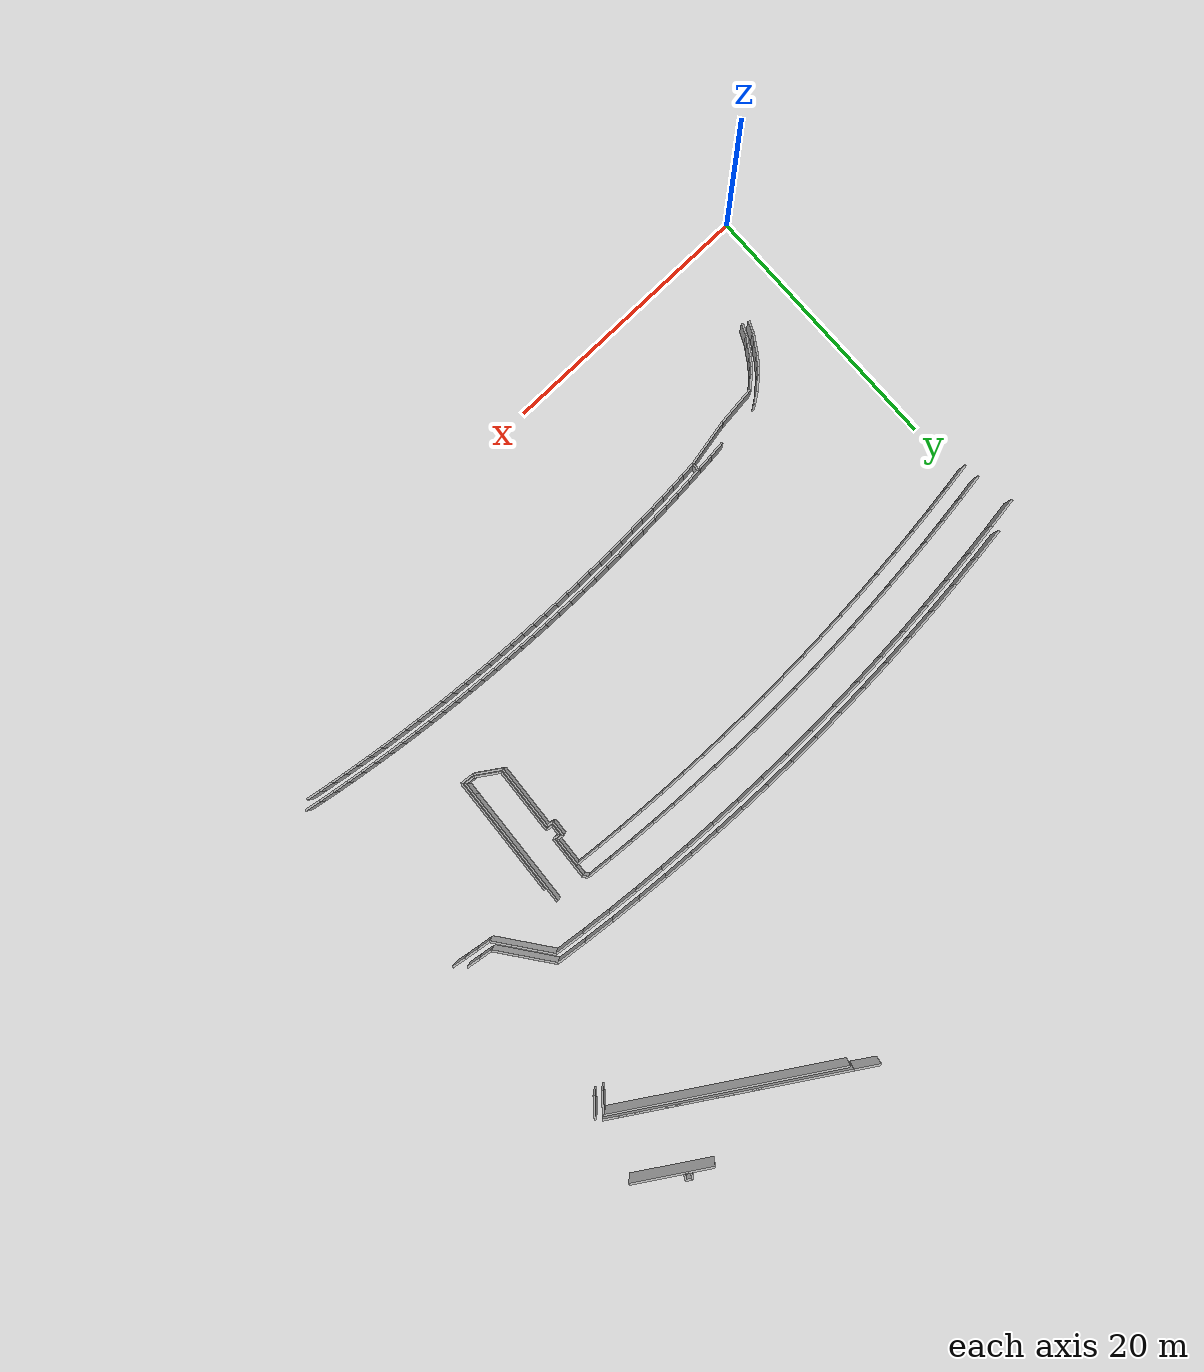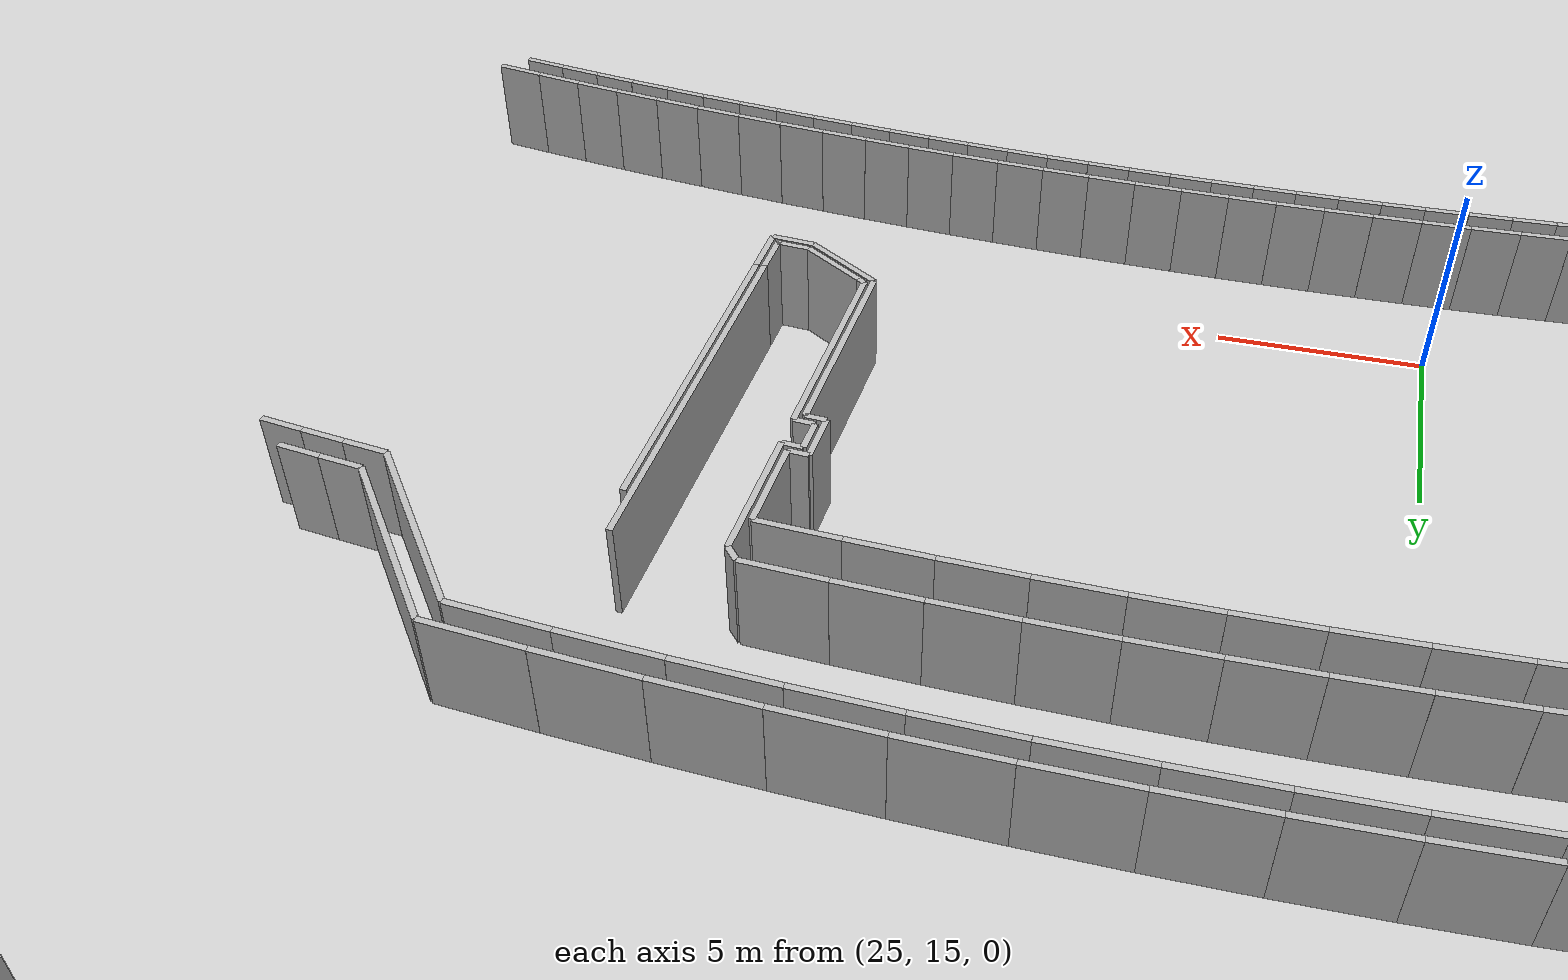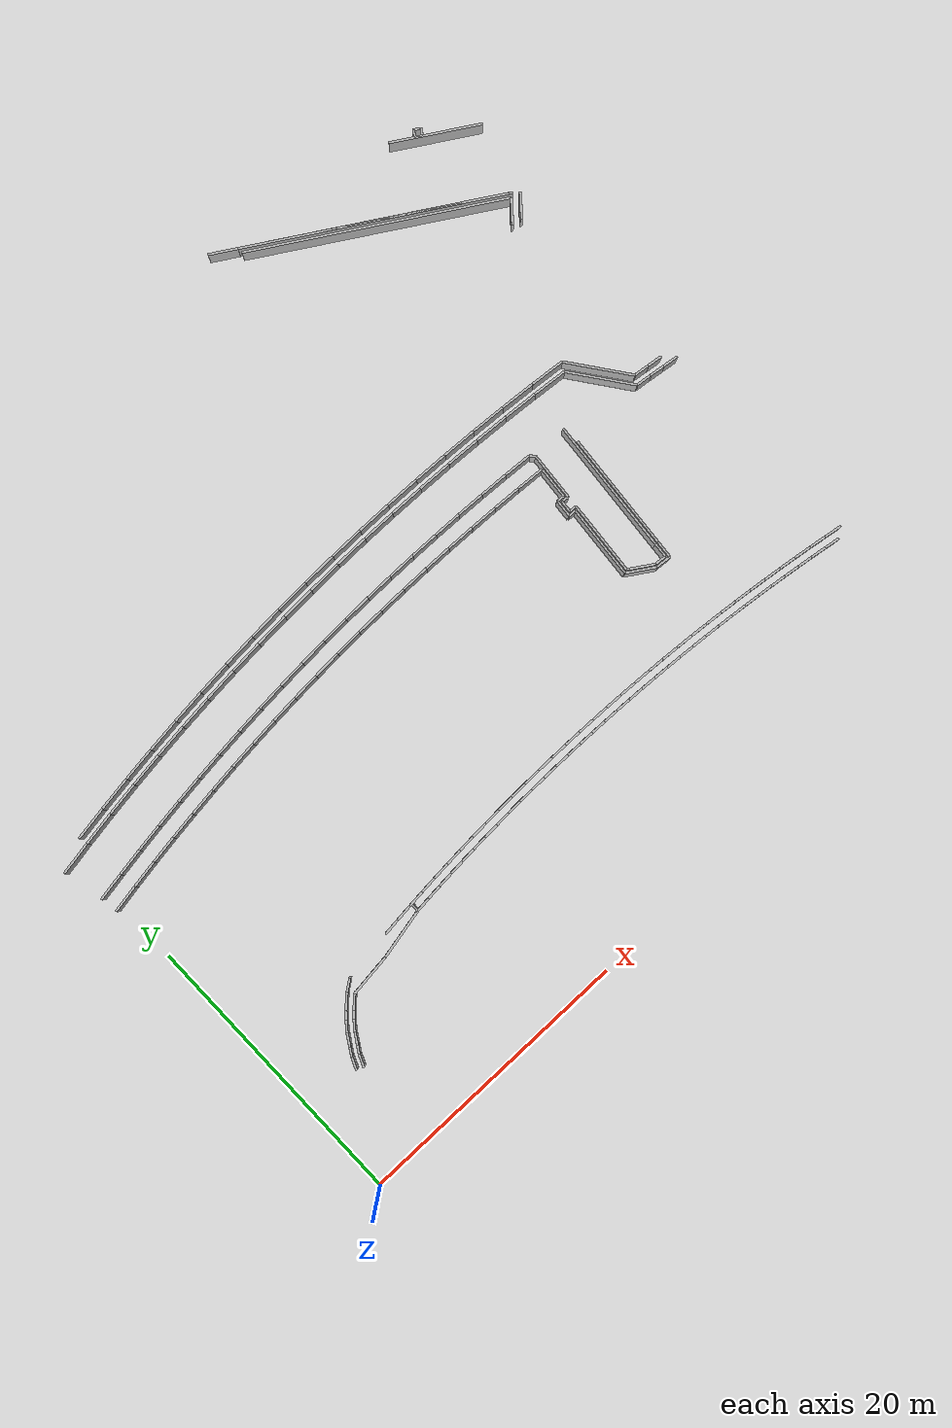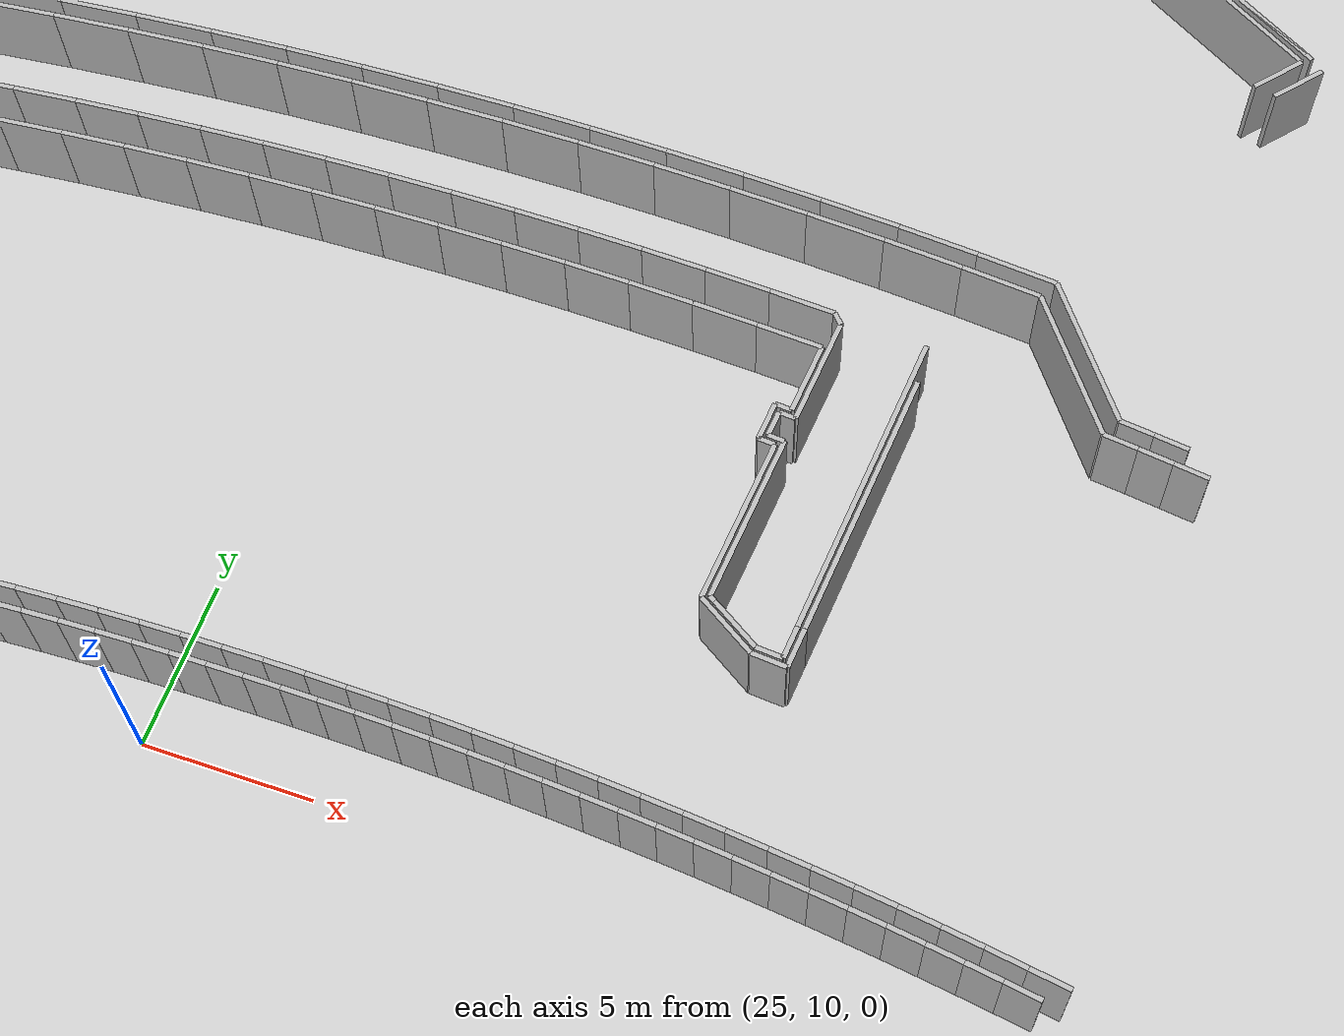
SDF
<?xml version="1.0" ?>
<sdf version="1.6">
  <model name="sps_0406">
    <pose frame="">0 0 0 0 -0 0</pose>
    <static>1</static>
    <self_collide>0</self_collide>
    <allow_auto_disable>0</allow_auto_disable>
    <link name="Wall71">
      <kinematic>0</kinematic>
      <gravity>1</gravity>
      <self_collide>0</self_collide>
      <collision name="collision">
        <geometry>
          <box>
            <size>0.421971 0.15 2.5</size>
          </box>
        </geometry>
        <pose frame="">0 0 0 0 -0 0</pose>
      </collision>
      <visual name="visual">
        <geometry>
          <box>
            <size>0.421971 0.15 2.5</size>
          </box>
        </geometry>
        <pose frame="">0 0 0 0 -0 0</pose>
        <cast_shadows>1</cast_shadows>
        <transparency>0.0</transparency>
      </visual>
      <pose frame="">39.1257 27.4712 1.25 0 0 -0.861464</pose>
    </link>
    <link name="Wall451">
      <kinematic>0</kinematic>
      <gravity>1</gravity>
      <self_collide>0</self_collide>
      <collision name="collision">
        <geometry>
          <box>
            <size>0.928626 0.15 2.5</size>
          </box>
        </geometry>
        <pose frame="">0 0 0 0 -0 0</pose>
      </collision>
      <visual name="visual">
        <geometry>
          <box>
            <size>0.928626 0.15 2.5</size>
          </box>
        </geometry>
        <pose frame="">0 0 0 0 -0 0</pose>
        <cast_shadows>1</cast_shadows>
        <transparency>0.0</transparency>
      </visual>
      <pose frame="">7.33526 10.7762 1.25 0 -0 0.629869</pose>
    </link>
    <link name="Wall462">
      <kinematic>0</kinematic>
      <gravity>1</gravity>
      <self_collide>0</self_collide>
      <collision name="collision">
        <geometry>
          <box>
            <size>2.24269 0.15 2.5</size>
          </box>
        </geometry>
        <pose frame="">0 0 0 0 -0 0</pose>
      </collision>
      <visual name="visual">
        <geometry>
          <box>
            <size>2.24269 0.15 2.5</size>
          </box>
        </geometry>
        <pose frame="">0 0 0 0 -0 0</pose>
        <cast_shadows>1</cast_shadows>
        <transparency>0.0</transparency>
      </visual>
      <pose frame="">38.8982 25.3099 1.25 0 0 -1.6524</pose>
    </link>
    <link name="Wall463">
      <kinematic>0</kinematic>
      <gravity>1</gravity>
      <self_collide>0</self_collide>
      <collision name="collision">
        <geometry>
          <box>
            <size>1.00034 0.15 2.5</size>
          </box>
        </geometry>
        <pose frame="">0 0 0 0 -0 0</pose>
      </collision>
      <visual name="visual">
        <geometry>
          <box>
            <size>1.00034 0.15 2.5</size>
          </box>
        </geometry>
        <pose frame="">0 0 0 0 -0 0</pose>
        <cast_shadows>1</cast_shadows>
        <transparency>0.0</transparency>
      </visual>
      <pose frame="">40.9593 17.3946 1.25 0 -0 1.48912</pose>
    </link>
    <link name="Wall464">
      <kinematic>0</kinematic>
      <gravity>1</gravity>
      <self_collide>0</self_collide>
      <collision name="collision">
        <geometry>
          <box>
            <size>9.54464 0.15 2.5</size>
          </box>
        </geometry>
        <pose frame="">0 0 0 0 -0 0</pose>
      </collision>
      <visual name="visual">
        <geometry>
          <box>
            <size>9.54464 0.15 2.5</size>
          </box>
        </geometry>
        <pose frame="">0 0 0 0 -0 0</pose>
        <cast_shadows>1</cast_shadows>
        <transparency>0.0</transparency>
      </visual>
      <pose frame="">41.3895 22.6495 1.25 0 -0 1.48912</pose>
    </link>
    <link name="Wall469">
      <kinematic>0</kinematic>
      <gravity>1</gravity>
      <self_collide>0</self_collide>
      <collision name="collision">
        <geometry>
          <box>
            <size>18.1378 0.15 2.5</size>
          </box>
        </geometry>
        <pose frame="">0 0 0 0 -0 0</pose>
      </collision>
      <visual name="visual">
        <geometry>
          <box>
            <size>18.1378 0.15 2.5</size>
          </box>
        </geometry>
        <pose frame="">0 0 0 0 -0 0</pose>
        <cast_shadows>1</cast_shadows>
        <transparency>0.0</transparency>
      </visual>
      <pose frame="">42.2045 45.6037 1.25 0 0 -0.549248</pose>
    </link>
    <link name="Wall805">
      <kinematic>0</kinematic>
      <gravity>1</gravity>
      <self_collide>0</self_collide>
      <collision name="collision">
        <geometry>
          <box>
            <size>1.20025 0.15 2.5</size>
          </box>
        </geometry>
        <pose frame="">0 0 0 0 -0 0</pose>
      </collision>
      <visual name="visual">
        <geometry>
          <box>
            <size>1.20025 0.15 2.5</size>
          </box>
        </geometry>
        <pose frame="">0 0 0 0 -0 0</pose>
        <cast_shadows>1</cast_shadows>
        <transparency>0.0</transparency>
      </visual>
      <pose frame="">38.2593 23.6358 1.25 0 0 -1.65271</pose>
    </link>
    <link name="Wall806">
      <kinematic>0</kinematic>
      <gravity>1</gravity>
      <self_collide>0</self_collide>
      <collision name="collision">
        <geometry>
          <box>
            <size>3.346 0.15 2.5</size>
          </box>
        </geometry>
        <pose frame="">0 0 0 0 -0 0</pose>
      </collision>
      <visual name="visual">
        <geometry>
          <box>
            <size>3.346 0.15 2.5</size>
          </box>
        </geometry>
        <pose frame="">0 0 0 0 -0 0</pose>
        <cast_shadows>1</cast_shadows>
        <transparency>0.0</transparency>
      </visual>
      <pose frame="">39.1266 25.6437 1.25 0 0 -1.65248</pose>
    </link>
    <link name="Wall808">
      <kinematic>0</kinematic>
      <gravity>1</gravity>
      <self_collide>0</self_collide>
      <collision name="collision">
        <geometry>
          <box>
            <size>17.8051 0.15 2.5</size>
          </box>
        </geometry>
        <pose frame="">0 0 0 0 -0 0</pose>
      </collision>
      <visual name="visual">
        <geometry>
          <box>
            <size>17.8051 0.15 2.5</size>
          </box>
        </geometry>
        <pose frame="">0 0 0 0 -0 0</pose>
        <cast_shadows>1</cast_shadows>
        <transparency>0.0</transparency>
      </visual>
      <pose frame="">42.0626 45.3383 1.25 0 0 -0.549258</pose>
    </link>
    <link name="Wall1203">
      <kinematic>0</kinematic>
      <gravity>1</gravity>
      <self_collide>0</self_collide>
      <collision name="collision">
        <geometry>
          <box>
            <size>2.09398 0.15 2.5</size>
          </box>
        </geometry>
        <pose frame="">0 0 0 0 -0 0</pose>
      </collision>
      <visual name="visual">
        <geometry>
          <box>
            <size>2.09398 0.15 2.5</size>
          </box>
        </geometry>
        <pose frame="">0 0 0 0 -0 0</pose>
        <cast_shadows>1</cast_shadows>
        <transparency>0.0</transparency>
      </visual>
      <pose frame="">39.1731 17.3294 1.25 0 -0 2.57307</pose>
    </link>
    <link name="Wall1205">
      <kinematic>0</kinematic>
      <gravity>1</gravity>
      <self_collide>0</self_collide>
      <collision name="collision">
        <geometry>
          <box>
            <size>1.04953 0.15 2.5</size>
          </box>
        </geometry>
        <pose frame="">0 0 0 0 -0 0</pose>
      </collision>
      <visual name="visual">
        <geometry>
          <box>
            <size>1.04953 0.15 2.5</size>
          </box>
        </geometry>
        <pose frame="">0 0 0 0 -0 0</pose>
        <cast_shadows>1</cast_shadows>
        <transparency>0.0</transparency>
      </visual>
      <pose frame="">40.5785 16.7228 1.25 0 -0 3.05974</pose>
    </link>
    <link name="Wall1518">
      <kinematic>0</kinematic>
      <gravity>1</gravity>
      <self_collide>0</self_collide>
      <collision name="collision">
        <geometry>
          <box>
            <size>1.80056 0.15 2.5</size>
          </box>
        </geometry>
        <pose frame="">0 0 0 0 -0 0</pose>
      </collision>
      <visual name="visual">
        <geometry>
          <box>
            <size>1.80056 0.15 2.5</size>
          </box>
        </geometry>
        <pose frame="">0 0 0 0 -0 0</pose>
        <cast_shadows>1</cast_shadows>
        <transparency>0.0</transparency>
      </visual>
      <pose frame="">49.7382 39.8607 1.25 0 0 -2.27316</pose>
    </link>
    <link name="Wall1820">
      <kinematic>0</kinematic>
      <gravity>1</gravity>
      <self_collide>0</self_collide>
      <collision name="collision">
        <geometry>
          <box>
            <size>5.1201 0.15 2.5</size>
          </box>
        </geometry>
        <pose frame="">0 0 0 0 -0 0</pose>
      </collision>
      <visual name="visual">
        <geometry>
          <box>
            <size>5.1201 0.15 2.5</size>
          </box>
        </geometry>
        <pose frame="">0 0 0 0 -0 0</pose>
        <cast_shadows>1</cast_shadows>
        <transparency>0.0</transparency>
      </visual>
      <pose frame="">38.4997 20.4446 1.25 0 -0 1.48911</pose>
    </link>
    <link name="Wall1821">
      <kinematic>0</kinematic>
      <gravity>1</gravity>
      <self_collide>0</self_collide>
      <collision name="collision">
        <geometry>
          <box>
            <size>0.500148 0.15 2.5</size>
          </box>
        </geometry>
        <pose frame="">0 0 0 0 -0 0</pose>
      </collision>
      <visual name="visual">
        <geometry>
          <box>
            <size>0.500148 0.15 2.5</size>
          </box>
        </geometry>
        <pose frame="">0 0 0 0 -0 0</pose>
        <cast_shadows>1</cast_shadows>
        <transparency>0.0</transparency>
      </visual>
      <pose frame="">38.5576 24.2131 1.25 0 -0 3.05827</pose>
    </link>
    <link name="Wall1822">
      <kinematic>0</kinematic>
      <gravity>1</gravity>
      <self_collide>0</self_collide>
      <collision name="collision">
        <geometry>
          <box>
            <size>0.500133 0.15 2.5</size>
          </box>
        </geometry>
        <pose frame="">0 0 0 0 -0 0</pose>
      </collision>
      <visual name="visual">
        <geometry>
          <box>
            <size>0.500133 0.15 2.5</size>
          </box>
        </geometry>
        <pose frame="">0 0 0 0 -0 0</pose>
        <cast_shadows>1</cast_shadows>
        <transparency>0.0</transparency>
      </visual>
      <pose frame="">38.7409 23.997 1.25 0 -0 3.05863</pose>
    </link>
    <link name="Wall1823">
      <kinematic>0</kinematic>
      <gravity>1</gravity>
      <self_collide>0</self_collide>
      <collision name="collision">
        <geometry>
          <box>
            <size>0.192513 0.15 2.5</size>
          </box>
        </geometry>
        <pose frame="">0 0 0 0 -0 0</pose>
      </collision>
      <visual name="visual">
        <geometry>
          <box>
            <size>0.192513 0.15 2.5</size>
          </box>
        </geometry>
        <pose frame="">0 0 0 0 -0 0</pose>
        <cast_shadows>1</cast_shadows>
        <transparency>0.0</transparency>
      </visual>
      <pose frame="">38.5814 17.9449 1.25 0 0 -0.568467</pose>
    </link>
    <link name="Wall1824">
      <kinematic>0</kinematic>
      <gravity>1</gravity>
      <self_collide>0</self_collide>
      <collision name="collision">
        <geometry>
          <box>
            <size>1.73126 0.15 2.5</size>
          </box>
        </geometry>
        <pose frame="">0 0 0 0 -0 0</pose>
      </collision>
      <visual name="visual">
        <geometry>
          <box>
            <size>1.73126 0.15 2.5</size>
          </box>
        </geometry>
        <pose frame="">0 0 0 0 -0 0</pose>
        <cast_shadows>1</cast_shadows>
        <transparency>0.0</transparency>
      </visual>
      <pose frame="">39.392 17.4271 1.25 0 0 -0.568467</pose>
    </link>
    <link name="Wall1827">
      <kinematic>0</kinematic>
      <gravity>1</gravity>
      <self_collide>0</self_collide>
      <collision name="collision">
        <geometry>
          <box>
            <size>4.78669 0.15 2.5</size>
          </box>
        </geometry>
        <pose frame="">0 0 0 0 -0 0</pose>
      </collision>
      <visual name="visual">
        <geometry>
          <box>
            <size>4.78669 0.15 2.5</size>
          </box>
        </geometry>
        <pose frame="">0 0 0 0 -0 0</pose>
        <cast_shadows>1</cast_shadows>
        <transparency>0.0</transparency>
      </visual>
      <pose frame="">46.1321 28.7068 1.25 0 0 -0.935844</pose>
    </link>
    <link name="Wall2146">
      <kinematic>0</kinematic>
      <gravity>1</gravity>
      <self_collide>0</self_collide>
      <collision name="collision">
        <geometry>
          <box>
            <size>3.03317 0.15 2.5</size>
          </box>
        </geometry>
        <pose frame="">0 0 0 0 -0 0</pose>
      </collision>
      <visual name="visual">
        <geometry>
          <box>
            <size>3.03317 0.15 2.5</size>
          </box>
        </geometry>
        <pose frame="">0 0 0 0 -0 0</pose>
        <cast_shadows>1</cast_shadows>
        <transparency>0.0</transparency>
      </visual>
      <pose frame="">8.74166 10.2674 1.25 0 -0 0.120362</pose>
    </link>
    <link name="Wall2148">
      <kinematic>0</kinematic>
      <gravity>1</gravity>
      <self_collide>0</self_collide>
      <collision name="collision">
        <geometry>
          <box>
            <size>0.59976 0.15 2.5</size>
          </box>
        </geometry>
        <pose frame="">0 0 0 0 -0 0</pose>
      </collision>
      <visual name="visual">
        <geometry>
          <box>
            <size>0.59976 0.15 2.5</size>
          </box>
        </geometry>
        <pose frame="">0 0 0 0 -0 0</pose>
        <cast_shadows>1</cast_shadows>
        <transparency>0.0</transparency>
      </visual>
      <pose frame="">13.7914 11.4866 1.25 0 -0 1.5204</pose>
    </link>
    <link name="Wall2160">
      <kinematic>0</kinematic>
      <gravity>1</gravity>
      <self_collide>0</self_collide>
      <collision name="collision">
        <geometry>
          <box>
            <size>0.500143 0.15 2.5</size>
          </box>
        </geometry>
        <pose frame="">0 0 0 0 -0 0</pose>
      </collision>
      <visual name="visual">
        <geometry>
          <box>
            <size>0.500143 0.15 2.5</size>
          </box>
        </geometry>
        <pose frame="">0 0 0 0 -0 0</pose>
        <cast_shadows>1</cast_shadows>
        <transparency>0.0</transparency>
      </visual>
      <pose frame="">38.4594 23.0169 1.25 0 0 -0.083202</pose>
    </link>
    <link name="Wall2161">
      <kinematic>0</kinematic>
      <gravity>1</gravity>
      <self_collide>0</self_collide>
      <collision name="collision">
        <geometry>
          <box>
            <size>0.500072 0.15 2.5</size>
          </box>
        </geometry>
        <pose frame="">0 0 0 0 -0 0</pose>
      </collision>
      <visual name="visual">
        <geometry>
          <box>
            <size>0.500072 0.15 2.5</size>
          </box>
        </geometry>
        <pose frame="">0 0 0 0 -0 0</pose>
        <cast_shadows>1</cast_shadows>
        <transparency>0.0</transparency>
      </visual>
      <pose frame="">38.6757 23.2 1.25 0 0 -0.0829689</pose>
    </link>
    <link name="Wall2162">
      <kinematic>0</kinematic>
      <gravity>1</gravity>
      <self_collide>0</self_collide>
      <collision name="collision">
        <geometry>
          <box>
            <size>0.799643 0.15 2.5</size>
          </box>
        </geometry>
        <pose frame="">0 0 0 0 -0 0</pose>
      </collision>
      <visual name="visual">
        <geometry>
          <box>
            <size>0.799643 0.15 2.5</size>
          </box>
        </geometry>
        <pose frame="">0 0 0 0 -0 0</pose>
        <cast_shadows>1</cast_shadows>
        <transparency>0.0</transparency>
      </visual>
      <pose frame="">40.52 16.9286 1.25 0 0 -0.0813791</pose>
    </link>
    <link name="Wall2163">
      <kinematic>0</kinematic>
      <gravity>1</gravity>
      <self_collide>0</self_collide>
      <collision name="collision">
        <geometry>
          <box>
            <size>8.32637 0.15 2.5</size>
          </box>
        </geometry>
        <pose frame="">0 0 0 0 -0 0</pose>
      </collision>
      <visual name="visual">
        <geometry>
          <box>
            <size>8.32637 0.15 2.5</size>
          </box>
        </geometry>
        <pose frame="">0 0 0 0 -0 0</pose>
        <cast_shadows>1</cast_shadows>
        <transparency>0.0</transparency>
      </visual>
      <pose frame="">41.5406 22.0424 1.25 0 0 -1.65251</pose>
    </link>
    <link name="Wall2164">
      <kinematic>0</kinematic>
      <gravity>1</gravity>
      <self_collide>0</self_collide>
      <collision name="collision">
        <geometry>
          <box>
            <size>1.21726 0.15 2.5</size>
          </box>
        </geometry>
        <pose frame="">0 0 0 0 -0 0</pose>
      </collision>
      <visual name="visual">
        <geometry>
          <box>
            <size>1.21726 0.15 2.5</size>
          </box>
        </geometry>
        <pose frame="">0 0 0 0 -0 0</pose>
        <cast_shadows>1</cast_shadows>
        <transparency>0.0</transparency>
      </visual>
      <pose frame="">41.1511 17.2865 1.25 0 0 -1.65251</pose>
    </link>
    <link name="Wall2537">
      <kinematic>0</kinematic>
      <gravity>1</gravity>
      <self_collide>0</self_collide>
      <collision name="collision">
        <geometry>
          <box>
            <size>3.60525 0.15 2.5</size>
          </box>
        </geometry>
        <pose frame="">0 0 0 0 -0 0</pose>
      </collision>
      <visual name="visual">
        <geometry>
          <box>
            <size>3.60525 0.15 2.5</size>
          </box>
        </geometry>
        <pose frame="">0 0 0 0 -0 0</pose>
        <cast_shadows>1</cast_shadows>
        <transparency>0.0</transparency>
      </visual>
      <pose frame="">12.0118 10.8183 1.25 0 -0 0.206048</pose>
    </link>
    <link name="Wall2546">
      <kinematic>0</kinematic>
      <gravity>1</gravity>
      <self_collide>0</self_collide>
      <collision name="collision">
        <geometry>
          <box>
            <size>0.799658 0.15 2.5</size>
          </box>
        </geometry>
        <pose frame="">0 0 0 0 -0 0</pose>
      </collision>
      <visual name="visual">
        <geometry>
          <box>
            <size>0.799658 0.15 2.5</size>
          </box>
        </geometry>
        <pose frame="">0 0 0 0 -0 0</pose>
        <cast_shadows>1</cast_shadows>
        <transparency>0.0</transparency>
      </visual>
      <pose frame="">38.4591 23.6192 1.25 0 0 -1.6524</pose>
    </link>
    <link name="Wall2547">
      <kinematic>0</kinematic>
      <gravity>1</gravity>
      <self_collide>0</self_collide>
      <collision name="collision">
        <geometry>
          <box>
            <size>5.19992 0.15 2.5</size>
          </box>
        </geometry>
        <pose frame="">0 0 0 0 -0 0</pose>
      </collision>
      <visual name="visual">
        <geometry>
          <box>
            <size>5.19992 0.15 2.5</size>
          </box>
        </geometry>
        <pose frame="">0 0 0 0 -0 0</pose>
        <cast_shadows>1</cast_shadows>
        <transparency>0.0</transparency>
      </visual>
      <pose frame="">38.7125 20.588 1.25 0 0 -1.65253</pose>
    </link>
    <link name="Wall2550">
      <kinematic>0</kinematic>
      <gravity>1</gravity>
      <self_collide>0</self_collide>
      <collision name="collision">
        <geometry>
          <box>
            <size>4.7795 0.15 2.5</size>
          </box>
        </geometry>
        <pose frame="">0 0 0 0 -0 0</pose>
      </collision>
      <visual name="visual">
        <geometry>
          <box>
            <size>4.7795 0.15 2.5</size>
          </box>
        </geometry>
        <pose frame="">0 0 0 0 -0 0</pose>
        <cast_shadows>1</cast_shadows>
        <transparency>0.0</transparency>
      </visual>
      <pose frame="">45.8034 28.141 1.25 0 0 -0.935925</pose>
    </link>
    <link name="Wall2551">
      <kinematic>0</kinematic>
      <gravity>1</gravity>
      <self_collide>0</self_collide>
      <collision name="collision">
        <geometry>
          <box>
            <size>1.78048 0.15 2.5</size>
          </box>
        </geometry>
        <pose frame="">0 0 0 0 -0 0</pose>
      </collision>
      <visual name="visual">
        <geometry>
          <box>
            <size>1.78048 0.15 2.5</size>
          </box>
        </geometry>
        <pose frame="">0 0 0 0 -0 0</pose>
        <cast_shadows>1</cast_shadows>
        <transparency>0.0</transparency>
      </visual>
      <pose frame="">49.0803 40.0114 1.25 0 0 -2.27359</pose>
    </link>
    <link name="Wall3039">
      <kinematic>0</kinematic>
      <gravity>1</gravity>
      <self_collide>0</self_collide>
      <collision name="collision">
        <geometry>
          <box>
            <size>3.09752 0.15 2.5</size>
          </box>
        </geometry>
        <pose frame="">0 0 0 0 -0 0</pose>
      </collision>
      <visual name="visual">
        <geometry>
          <box>
            <size>3.09752 0.15 2.5</size>
          </box>
        </geometry>
        <pose frame="">0 0 0 0 -0 0</pose>
        <cast_shadows>1</cast_shadows>
        <transparency>0.0</transparency>
      </visual>
      <pose frame="">48.3874 41.8201 1.25 0 -0 2.59229</pose>
    </link>
    <link name="Wall3040">
      <kinematic>0</kinematic>
      <gravity>1</gravity>
      <self_collide>0</self_collide>
      <collision name="collision">
        <geometry>
          <box>
            <size>3.67119 0.15 2.5</size>
          </box>
        </geometry>
        <pose frame="">0 0 0 0 -0 0</pose>
      </collision>
      <visual name="visual">
        <geometry>
          <box>
            <size>3.67119 0.15 2.5</size>
          </box>
        </geometry>
        <pose frame="">0 0 0 0 -0 0</pose>
        <cast_shadows>1</cast_shadows>
        <transparency>0.0</transparency>
      </visual>
      <pose frame="">45.5008 43.587 1.25 0 -0 2.59231</pose>
    </link>
    <link name="Wall3041">
      <kinematic>0</kinematic>
      <gravity>1</gravity>
      <self_collide>0</self_collide>
      <collision name="collision">
        <geometry>
          <box>
            <size>3.34159 0.15 2.5</size>
          </box>
        </geometry>
        <pose frame="">0 0 0 0 -0 0</pose>
      </collision>
      <visual name="visual">
        <geometry>
          <box>
            <size>3.34159 0.15 2.5</size>
          </box>
        </geometry>
        <pose frame="">0 0 0 0 -0 0</pose>
        <cast_shadows>1</cast_shadows>
        <transparency>0.0</transparency>
      </visual>
      <pose frame="">42.5102 45.4176 1.25 0 -0 2.59231</pose>
    </link>
    <link name="Wall3042">
      <kinematic>0</kinematic>
      <gravity>1</gravity>
      <self_collide>0</self_collide>
      <collision name="collision">
        <geometry>
          <box>
            <size>1.14589 0.15 2.5</size>
          </box>
        </geometry>
        <pose frame="">0 0 0 0 -0 0</pose>
      </collision>
      <visual name="visual">
        <geometry>
          <box>
            <size>1.14589 0.15 2.5</size>
          </box>
        </geometry>
        <pose frame="">0 0 0 0 -0 0</pose>
        <cast_shadows>1</cast_shadows>
        <transparency>0.0</transparency>
      </visual>
      <pose frame="">40.5965 46.589 1.25 0 -0 2.59235</pose>
    </link>
    <link name="Wall3043">
      <kinematic>0</kinematic>
      <gravity>1</gravity>
      <self_collide>0</self_collide>
      <collision name="collision">
        <geometry>
          <box>
            <size>8.5971 0.15 2.5</size>
          </box>
        </geometry>
        <pose frame="">0 0 0 0 -0 0</pose>
      </collision>
      <visual name="visual">
        <geometry>
          <box>
            <size>8.5971 0.15 2.5</size>
          </box>
        </geometry>
        <pose frame="">0 0 0 0 -0 0</pose>
        <cast_shadows>1</cast_shadows>
        <transparency>0.0</transparency>
      </visual>
      <pose frame="">36.4416 49.1321 1.25 0 -0 2.59235</pose>
    </link>
    <link name="Wall6654">
      <kinematic>0</kinematic>
      <gravity>1</gravity>
      <self_collide>0</self_collide>
      <collision name="collision">
        <geometry>
          <box>
            <size>1.15065 0.15 2.5</size>
          </box>
        </geometry>
        <pose frame="">0 0 0 0 -0 0</pose>
      </collision>
      <visual name="visual">
        <geometry>
          <box>
            <size>1.15065 0.15 2.5</size>
          </box>
        </geometry>
        <pose frame="">0 0 0 0 -0 0</pose>
        <cast_shadows>1</cast_shadows>
        <transparency>0.0</transparency>
      </visual>
      <pose frame="">6.54214 10.1073 1.25 0 0 -2.38384</pose>
    </link>
    <link name="Wall6655">
      <kinematic>0</kinematic>
      <gravity>1</gravity>
      <self_collide>0</self_collide>
      <collision name="collision">
        <geometry>
          <box>
            <size>0.595889 0.15 2.5</size>
          </box>
        </geometry>
        <pose frame="">0 0 0 0 -0 0</pose>
      </collision>
      <visual name="visual">
        <geometry>
          <box>
            <size>0.595889 0.15 2.5</size>
          </box>
        </geometry>
        <pose frame="">0 0 0 0 -0 0</pose>
        <cast_shadows>1</cast_shadows>
        <transparency>0.0</transparency>
      </visual>
      <pose frame="">5.92394 9.49129 1.25 0 0 -2.30801</pose>
    </link>
    <link name="Wall6656">
      <kinematic>0</kinematic>
      <gravity>1</gravity>
      <self_collide>0</self_collide>
      <collision name="collision">
        <geometry>
          <box>
            <size>0.803346 0.15 2.5</size>
          </box>
        </geometry>
        <pose frame="">0 0 0 0 -0 0</pose>
      </collision>
      <visual name="visual">
        <geometry>
          <box>
            <size>0.803346 0.15 2.5</size>
          </box>
        </geometry>
        <pose frame="">0 0 0 0 -0 0</pose>
        <cast_shadows>1</cast_shadows>
        <transparency>0.0</transparency>
      </visual>
      <pose frame="">5.47304 8.9568 1.25 0 0 -2.24454</pose>
    </link>
    <link name="Wall6657">
      <kinematic>0</kinematic>
      <gravity>1</gravity>
      <self_collide>0</self_collide>
      <collision name="collision">
        <geometry>
          <box>
            <size>0.947839 0.15 2.5</size>
          </box>
        </geometry>
        <pose frame="">0 0 0 0 -0 0</pose>
      </collision>
      <visual name="visual">
        <geometry>
          <box>
            <size>0.947839 0.15 2.5</size>
          </box>
        </geometry>
        <pose frame="">0 0 0 0 -0 0</pose>
        <cast_shadows>1</cast_shadows>
        <transparency>0.0</transparency>
      </visual>
      <pose frame="">4.97146 8.24089 1.25 0 0 -2.1289</pose>
    </link>
    <link name="Wall6658">
      <kinematic>0</kinematic>
      <gravity>1</gravity>
      <self_collide>0</self_collide>
      <collision name="collision">
        <geometry>
          <box>
            <size>0.612831 0.15 2.5</size>
          </box>
        </geometry>
        <pose frame="">0 0 0 0 -0 0</pose>
      </collision>
      <visual name="visual">
        <geometry>
          <box>
            <size>0.612831 0.15 2.5</size>
          </box>
        </geometry>
        <pose frame="">0 0 0 0 -0 0</pose>
        <cast_shadows>1</cast_shadows>
        <transparency>0.0</transparency>
      </visual>
      <pose frame="">4.55816 7.57899 1.25 0 0 -2.1291</pose>
    </link>
    <link name="Wall6659">
      <kinematic>0</kinematic>
      <gravity>1</gravity>
      <self_collide>0</self_collide>
      <collision name="collision">
        <geometry>
          <box>
            <size>0.921616 0.15 2.5</size>
          </box>
        </geometry>
        <pose frame="">0 0 0 0 -0 0</pose>
      </collision>
      <visual name="visual">
        <geometry>
          <box>
            <size>0.921616 0.15 2.5</size>
          </box>
        </geometry>
        <pose frame="">0 0 0 0 -0 0</pose>
        <cast_shadows>1</cast_shadows>
        <transparency>0.0</transparency>
      </visual>
      <pose frame="">4.21633 6.8947 1.25 0 0 -1.97093</pose>
    </link>
    <link name="Wall6675">
      <kinematic>0</kinematic>
      <gravity>1</gravity>
      <self_collide>0</self_collide>
      <collision name="collision">
        <geometry>
          <box>
            <size>1.98001 0.15 2.5</size>
          </box>
        </geometry>
        <pose frame="">0 0 0 0 -0 0</pose>
      </collision>
      <visual name="visual">
        <geometry>
          <box>
            <size>1.98001 0.15 2.5</size>
          </box>
        </geometry>
        <pose frame="">0 0 0 0 -0 0</pose>
        <cast_shadows>1</cast_shadows>
        <transparency>0.0</transparency>
      </visual>
      <pose frame="">38.0004 27.6961 1.25 0 -0 3.0761</pose>
    </link>
    <link name="Wall6676">
      <kinematic>0</kinematic>
      <gravity>1</gravity>
      <self_collide>0</self_collide>
      <collision name="collision">
        <geometry>
          <box>
            <size>1.98001 0.15 2.5</size>
          </box>
        </geometry>
        <pose frame="">0 0 0 0 -0 0</pose>
      </collision>
      <visual name="visual">
        <geometry>
          <box>
            <size>1.98001 0.15 2.5</size>
          </box>
        </geometry>
        <pose frame="">0 0 0 0 -0 0</pose>
        <cast_shadows>1</cast_shadows>
        <transparency>0.0</transparency>
      </visual>
      <pose frame="">36.0239 27.8133 1.25 0 -0 3.08864</pose>
    </link>
    <link name="Wall6677">
      <kinematic>0</kinematic>
      <gravity>1</gravity>
      <self_collide>0</self_collide>
      <collision name="collision">
        <geometry>
          <box>
            <size>1.97983 0.15 2.5</size>
          </box>
        </geometry>
        <pose frame="">0 0 0 0 -0 0</pose>
      </collision>
      <visual name="visual">
        <geometry>
          <box>
            <size>1.97983 0.15 2.5</size>
          </box>
        </geometry>
        <pose frame="">0 0 0 0 -0 0</pose>
        <cast_shadows>1</cast_shadows>
        <transparency>0.0</transparency>
      </visual>
      <pose frame="">34.0461 27.9057 1.25 0 -0 3.10117</pose>
    </link>
    <link name="Wall6678">
      <kinematic>0</kinematic>
      <gravity>1</gravity>
      <self_collide>0</self_collide>
      <collision name="collision">
        <geometry>
          <box>
            <size>1.97997 0.15 2.5</size>
          </box>
        </geometry>
        <pose frame="">0 0 0 0 -0 0</pose>
      </collision>
      <visual name="visual">
        <geometry>
          <box>
            <size>1.97997 0.15 2.5</size>
          </box>
        </geometry>
        <pose frame="">0 0 0 0 -0 0</pose>
        <cast_shadows>1</cast_shadows>
        <transparency>0.0</transparency>
      </visual>
      <pose frame="">32.0674 27.9735 1.25 0 -0 3.11351</pose>
    </link>
    <link name="Wall6679">
      <kinematic>0</kinematic>
      <gravity>1</gravity>
      <self_collide>0</self_collide>
      <collision name="collision">
        <geometry>
          <box>
            <size>1.98004 0.15 2.5</size>
          </box>
        </geometry>
        <pose frame="">0 0 0 0 -0 0</pose>
      </collision>
      <visual name="visual">
        <geometry>
          <box>
            <size>1.98004 0.15 2.5</size>
          </box>
        </geometry>
        <pose frame="">0 0 0 0 -0 0</pose>
        <cast_shadows>1</cast_shadows>
        <transparency>0.0</transparency>
      </visual>
      <pose frame="">30.0879 28.0167 1.25 0 -0 3.12603</pose>
    </link>
    <link name="Wall6680">
      <kinematic>0</kinematic>
      <gravity>1</gravity>
      <self_collide>0</self_collide>
      <collision name="collision">
        <geometry>
          <box>
            <size>1.97999 0.15 2.5</size>
          </box>
        </geometry>
        <pose frame="">0 0 0 0 -0 0</pose>
      </collision>
      <visual name="visual">
        <geometry>
          <box>
            <size>1.97999 0.15 2.5</size>
          </box>
        </geometry>
        <pose frame="">0 0 0 0 -0 0</pose>
        <cast_shadows>1</cast_shadows>
        <transparency>0.0</transparency>
      </visual>
      <pose frame="">28.1081 28.0351 1.25 0 -0 3.13857</pose>
    </link>
    <link name="Wall6681">
      <kinematic>0</kinematic>
      <gravity>1</gravity>
      <self_collide>0</self_collide>
      <collision name="collision">
        <geometry>
          <box>
            <size>1.97989 0.15 2.5</size>
          </box>
        </geometry>
        <pose frame="">0 0 0 0 -0 0</pose>
      </collision>
      <visual name="visual">
        <geometry>
          <box>
            <size>1.97989 0.15 2.5</size>
          </box>
        </geometry>
        <pose frame="">0 0 0 0 -0 0</pose>
        <cast_shadows>1</cast_shadows>
        <transparency>0.0</transparency>
      </visual>
      <pose frame="">26.1282 28.0286 1.25 0 0 -3.13201</pose>
    </link>
    <link name="Wall6682">
      <kinematic>0</kinematic>
      <gravity>1</gravity>
      <self_collide>0</self_collide>
      <collision name="collision">
        <geometry>
          <box>
            <size>1.9801 0.15 2.5</size>
          </box>
        </geometry>
        <pose frame="">0 0 0 0 -0 0</pose>
      </collision>
      <visual name="visual">
        <geometry>
          <box>
            <size>1.9801 0.15 2.5</size>
          </box>
        </geometry>
        <pose frame="">0 0 0 0 -0 0</pose>
        <cast_shadows>1</cast_shadows>
        <transparency>0.0</transparency>
      </visual>
      <pose frame="">24.1485 27.9973 1.25 0 0 -3.11955</pose>
    </link>
    <link name="Wall6683">
      <kinematic>0</kinematic>
      <gravity>1</gravity>
      <self_collide>0</self_collide>
      <collision name="collision">
        <geometry>
          <box>
            <size>1.98001 0.15 2.5</size>
          </box>
        </geometry>
        <pose frame="">0 0 0 0 -0 0</pose>
      </collision>
      <visual name="visual">
        <geometry>
          <box>
            <size>1.98001 0.15 2.5</size>
          </box>
        </geometry>
        <pose frame="">0 0 0 0 -0 0</pose>
        <cast_shadows>1</cast_shadows>
        <transparency>0.0</transparency>
      </visual>
      <pose frame="">22.1692 27.9412 1.25 0 0 -3.10694</pose>
    </link>
    <link name="Wall6684">
      <kinematic>0</kinematic>
      <gravity>1</gravity>
      <self_collide>0</self_collide>
      <collision name="collision">
        <geometry>
          <box>
            <size>1.9798 0.15 2.5</size>
          </box>
        </geometry>
        <pose frame="">0 0 0 0 -0 0</pose>
      </collision>
      <visual name="visual">
        <geometry>
          <box>
            <size>1.9798 0.15 2.5</size>
          </box>
        </geometry>
        <pose frame="">0 0 0 0 -0 0</pose>
        <cast_shadows>1</cast_shadows>
        <transparency>0.0</transparency>
      </visual>
      <pose frame="">20.191 27.8603 1.25 0 0 -3.0945</pose>
    </link>
    <link name="Wall6685">
      <kinematic>0</kinematic>
      <gravity>1</gravity>
      <self_collide>0</self_collide>
      <collision name="collision">
        <geometry>
          <box>
            <size>1.97991 0.15 2.5</size>
          </box>
        </geometry>
        <pose frame="">0 0 0 0 -0 0</pose>
      </collision>
      <visual name="visual">
        <geometry>
          <box>
            <size>1.97991 0.15 2.5</size>
          </box>
        </geometry>
        <pose frame="">0 0 0 0 -0 0</pose>
        <cast_shadows>1</cast_shadows>
        <transparency>0.0</transparency>
      </visual>
      <pose frame="">18.214 27.7546 1.25 0 0 -3.08188</pose>
    </link>
    <link name="Wall6686">
      <kinematic>0</kinematic>
      <gravity>1</gravity>
      <self_collide>0</self_collide>
      <collision name="collision">
        <geometry>
          <box>
            <size>1.97994 0.15 2.5</size>
          </box>
        </geometry>
        <pose frame="">0 0 0 0 -0 0</pose>
      </collision>
      <visual name="visual">
        <geometry>
          <box>
            <size>1.97994 0.15 2.5</size>
          </box>
        </geometry>
        <pose frame="">0 0 0 0 -0 0</pose>
        <cast_shadows>1</cast_shadows>
        <transparency>0.0</transparency>
      </visual>
      <pose frame="">16.2385 27.6242 1.25 0 0 -3.06949</pose>
    </link>
    <link name="Wall6687">
      <kinematic>0</kinematic>
      <gravity>1</gravity>
      <self_collide>0</self_collide>
      <collision name="collision">
        <geometry>
          <box>
            <size>1.97989 0.15 2.5</size>
          </box>
        </geometry>
        <pose frame="">0 0 0 0 -0 0</pose>
      </collision>
      <visual name="visual">
        <geometry>
          <box>
            <size>1.97989 0.15 2.5</size>
          </box>
        </geometry>
        <pose frame="">0 0 0 0 -0 0</pose>
        <cast_shadows>1</cast_shadows>
        <transparency>0.0</transparency>
      </visual>
      <pose frame="">14.2647 27.4691 1.25 0 0 -3.05684</pose>
    </link>
    <link name="Wall6688">
      <kinematic>0</kinematic>
      <gravity>1</gravity>
      <self_collide>0</self_collide>
      <collision name="collision">
        <geometry>
          <box>
            <size>1.97999 0.15 2.5</size>
          </box>
        </geometry>
        <pose frame="">0 0 0 0 -0 0</pose>
      </collision>
      <visual name="visual">
        <geometry>
          <box>
            <size>1.97999 0.15 2.5</size>
          </box>
        </geometry>
        <pose frame="">0 0 0 0 -0 0</pose>
        <cast_shadows>1</cast_shadows>
        <transparency>0.0</transparency>
      </visual>
      <pose frame="">12.293 27.2892 1.25 0 0 -3.04437</pose>
    </link>
    <link name="Wall6689">
      <kinematic>0</kinematic>
      <gravity>1</gravity>
      <self_collide>0</self_collide>
      <collision name="collision">
        <geometry>
          <box>
            <size>1.98012 0.15 2.5</size>
          </box>
        </geometry>
        <pose frame="">0 0 0 0 -0 0</pose>
      </collision>
      <visual name="visual">
        <geometry>
          <box>
            <size>1.98012 0.15 2.5</size>
          </box>
        </geometry>
        <pose frame="">0 0 0 0 -0 0</pose>
        <cast_shadows>1</cast_shadows>
        <transparency>0.0</transparency>
      </visual>
      <pose frame="">10.3235 27.0846 1.25 0 0 -3.03179</pose>
    </link>
    <link name="Wall6690">
      <kinematic>0</kinematic>
      <gravity>1</gravity>
      <self_collide>0</self_collide>
      <collision name="collision">
        <geometry>
          <box>
            <size>1.97998 0.15 2.5</size>
          </box>
        </geometry>
        <pose frame="">0 0 0 0 -0 0</pose>
      </collision>
      <visual name="visual">
        <geometry>
          <box>
            <size>1.97998 0.15 2.5</size>
          </box>
        </geometry>
        <pose frame="">0 0 0 0 -0 0</pose>
        <cast_shadows>1</cast_shadows>
        <transparency>0.0</transparency>
      </visual>
      <pose frame="">8.35683 26.8554 1.25 0 0 -3.01937</pose>
    </link>
    <link name="Wall6691">
      <kinematic>0</kinematic>
      <gravity>1</gravity>
      <self_collide>0</self_collide>
      <collision name="collision">
        <geometry>
          <box>
            <size>1.97995 0.15 2.5</size>
          </box>
        </geometry>
        <pose frame="">0 0 0 0 -0 0</pose>
      </collision>
      <visual name="visual">
        <geometry>
          <box>
            <size>1.97995 0.15 2.5</size>
          </box>
        </geometry>
        <pose frame="">0 0 0 0 -0 0</pose>
        <cast_shadows>1</cast_shadows>
        <transparency>0.0</transparency>
      </visual>
      <pose frame="">6.39324 26.6016 1.25 0 0 -3.00675</pose>
    </link>
    <link name="Wall6692">
      <kinematic>0</kinematic>
      <gravity>1</gravity>
      <self_collide>0</self_collide>
      <collision name="collision">
        <geometry>
          <box>
            <size>1.98009 0.15 2.5</size>
          </box>
        </geometry>
        <pose frame="">0 0 0 0 -0 0</pose>
      </collision>
      <visual name="visual">
        <geometry>
          <box>
            <size>1.98009 0.15 2.5</size>
          </box>
        </geometry>
        <pose frame="">0 0 0 0 -0 0</pose>
        <cast_shadows>1</cast_shadows>
        <transparency>0.0</transparency>
      </visual>
      <pose frame="">4.43294 26.3231 1.25 0 0 -2.99418</pose>
    </link>
    <link name="Wall6693">
      <kinematic>0</kinematic>
      <gravity>1</gravity>
      <self_collide>0</self_collide>
      <collision name="collision">
        <geometry>
          <box>
            <size>1.97984 0.15 2.5</size>
          </box>
        </geometry>
        <pose frame="">0 0 0 0 -0 0</pose>
      </collision>
      <visual name="visual">
        <geometry>
          <box>
            <size>1.97984 0.15 2.5</size>
          </box>
        </geometry>
        <pose frame="">0 0 0 0 -0 0</pose>
        <cast_shadows>1</cast_shadows>
        <transparency>0.0</transparency>
      </visual>
      <pose frame="">2.47634 26.0201 1.25 0 0 -2.98171</pose>
    </link>
    <link name="Wall6694">
      <kinematic>0</kinematic>
      <gravity>1</gravity>
      <self_collide>0</self_collide>
      <collision name="collision">
        <geometry>
          <box>
            <size>1.97993 0.15 2.5</size>
          </box>
        </geometry>
        <pose frame="">0 0 0 0 -0 0</pose>
      </collision>
      <visual name="visual">
        <geometry>
          <box>
            <size>1.97993 0.15 2.5</size>
          </box>
        </geometry>
        <pose frame="">0 0 0 0 -0 0</pose>
        <cast_shadows>1</cast_shadows>
        <transparency>0.0</transparency>
      </visual>
      <pose frame="">0.523765 25.6926 1.25 0 0 -2.96913</pose>
    </link>
    <link name="Wall6795">
      <kinematic>0</kinematic>
      <gravity>1</gravity>
      <self_collide>0</self_collide>
      <collision name="collision">
        <geometry>
          <box>
            <size>6.22606 0.15 2.5</size>
          </box>
        </geometry>
        <pose frame="">0 0 0 0 -0 0</pose>
      </collision>
      <visual name="visual">
        <geometry>
          <box>
            <size>6.22606 0.15 2.5</size>
          </box>
        </geometry>
        <pose frame="">0 0 0 0 -0 0</pose>
        <cast_shadows>1</cast_shadows>
        <transparency>0.0</transparency>
      </visual>
      <pose frame="">48.9723 47.1047 1.25 0 -0 2.59157</pose>
    </link>
    <link name="Wall6811">
      <kinematic>0</kinematic>
      <gravity>1</gravity>
      <self_collide>0</self_collide>
      <collision name="collision">
        <geometry>
          <box>
            <size>1.19264 0.15 2.5</size>
          </box>
        </geometry>
        <pose frame="">0 0 0 0 -0 0</pose>
      </collision>
      <visual name="visual">
        <geometry>
          <box>
            <size>1.19264 0.15 2.5</size>
          </box>
        </geometry>
        <pose frame="">0 0 0 0 -0 0</pose>
        <cast_shadows>1</cast_shadows>
        <transparency>0.0</transparency>
      </visual>
      <pose frame="">49.8899 10.7001 1.25 0 -0 2.98466</pose>
    </link>
    <link name="Wall6812">
      <kinematic>0</kinematic>
      <gravity>1</gravity>
      <self_collide>0</self_collide>
      <collision name="collision">
        <geometry>
          <box>
            <size>1.1925 0.15 2.5</size>
          </box>
        </geometry>
        <pose frame="">0 0 0 0 -0 0</pose>
      </collision>
      <visual name="visual">
        <geometry>
          <box>
            <size>1.1925 0.15 2.5</size>
          </box>
        </geometry>
        <pose frame="">0 0 0 0 -0 0</pose>
        <cast_shadows>1</cast_shadows>
        <transparency>0.0</transparency>
      </visual>
      <pose frame="">48.7112 10.8815 1.25 0 -0 2.99313</pose>
    </link>
    <link name="Wall6813">
      <kinematic>0</kinematic>
      <gravity>1</gravity>
      <self_collide>0</self_collide>
      <collision name="collision">
        <geometry>
          <box>
            <size>1.19252 0.15 2.5</size>
          </box>
        </geometry>
        <pose frame="">0 0 0 0 -0 0</pose>
      </collision>
      <visual name="visual">
        <geometry>
          <box>
            <size>1.19252 0.15 2.5</size>
          </box>
        </geometry>
        <pose frame="">0 0 0 0 -0 0</pose>
        <cast_shadows>1</cast_shadows>
        <transparency>0.0</transparency>
      </visual>
      <pose frame="">47.5311 11.0529 1.25 0 -0 3.00156</pose>
    </link>
    <link name="Wall6814">
      <kinematic>0</kinematic>
      <gravity>1</gravity>
      <self_collide>0</self_collide>
      <collision name="collision">
        <geometry>
          <box>
            <size>1.19254 0.15 2.5</size>
          </box>
        </geometry>
        <pose frame="">0 0 0 0 -0 0</pose>
      </collision>
      <visual name="visual">
        <geometry>
          <box>
            <size>1.19254 0.15 2.5</size>
          </box>
        </geometry>
        <pose frame="">0 0 0 0 -0 0</pose>
        <cast_shadows>1</cast_shadows>
        <transparency>0.0</transparency>
      </visual>
      <pose frame="">46.3495 11.2145 1.25 0 -0 3.00973</pose>
    </link>
    <link name="Wall6815">
      <kinematic>0</kinematic>
      <gravity>1</gravity>
      <self_collide>0</self_collide>
      <collision name="collision">
        <geometry>
          <box>
            <size>1.19248 0.15 2.5</size>
          </box>
        </geometry>
        <pose frame="">0 0 0 0 -0 0</pose>
      </collision>
      <visual name="visual">
        <geometry>
          <box>
            <size>1.19248 0.15 2.5</size>
          </box>
        </geometry>
        <pose frame="">0 0 0 0 -0 0</pose>
        <cast_shadows>1</cast_shadows>
        <transparency>0.0</transparency>
      </visual>
      <pose frame="">45.1667 11.3663 1.25 0 -0 3.01818</pose>
    </link>
    <link name="Wall6816">
      <kinematic>0</kinematic>
      <gravity>1</gravity>
      <self_collide>0</self_collide>
      <collision name="collision">
        <geometry>
          <box>
            <size>1.19262 0.15 2.5</size>
          </box>
        </geometry>
        <pose frame="">0 0 0 0 -0 0</pose>
      </collision>
      <visual name="visual">
        <geometry>
          <box>
            <size>1.19262 0.15 2.5</size>
          </box>
        </geometry>
        <pose frame="">0 0 0 0 -0 0</pose>
        <cast_shadows>1</cast_shadows>
        <transparency>0.0</transparency>
      </visual>
      <pose frame="">43.9827 11.5081 1.25 0 -0 3.02665</pose>
    </link>
    <link name="Wall6817">
      <kinematic>0</kinematic>
      <gravity>1</gravity>
      <self_collide>0</self_collide>
      <collision name="collision">
        <geometry>
          <box>
            <size>1.19263 0.15 2.5</size>
          </box>
        </geometry>
        <pose frame="">0 0 0 0 -0 0</pose>
      </collision>
      <visual name="visual">
        <geometry>
          <box>
            <size>1.19263 0.15 2.5</size>
          </box>
        </geometry>
        <pose frame="">0 0 0 0 -0 0</pose>
        <cast_shadows>1</cast_shadows>
        <transparency>0.0</transparency>
      </visual>
      <pose frame="">42.7974 11.64 1.25 0 -0 3.03489</pose>
    </link>
    <link name="Wall6818">
      <kinematic>0</kinematic>
      <gravity>1</gravity>
      <self_collide>0</self_collide>
      <collision name="collision">
        <geometry>
          <box>
            <size>1.1927 0.15 2.5</size>
          </box>
        </geometry>
        <pose frame="">0 0 0 0 -0 0</pose>
      </collision>
      <visual name="visual">
        <geometry>
          <box>
            <size>1.1927 0.15 2.5</size>
          </box>
        </geometry>
        <pose frame="">0 0 0 0 -0 0</pose>
        <cast_shadows>1</cast_shadows>
        <transparency>0.0</transparency>
      </visual>
      <pose frame="">41.611 11.762 1.25 0 -0 3.04333</pose>
    </link>
    <link name="Wall6819">
      <kinematic>0</kinematic>
      <gravity>1</gravity>
      <self_collide>0</self_collide>
      <collision name="collision">
        <geometry>
          <box>
            <size>1.19261 0.15 2.5</size>
          </box>
        </geometry>
        <pose frame="">0 0 0 0 -0 0</pose>
      </collision>
      <visual name="visual">
        <geometry>
          <box>
            <size>1.19261 0.15 2.5</size>
          </box>
        </geometry>
        <pose frame="">0 0 0 0 -0 0</pose>
        <cast_shadows>1</cast_shadows>
        <transparency>0.0</transparency>
      </visual>
      <pose frame="">40.4236 11.874 1.25 0 -0 3.05176</pose>
    </link>
    <link name="Wall6820">
      <kinematic>0</kinematic>
      <gravity>1</gravity>
      <self_collide>0</self_collide>
      <collision name="collision">
        <geometry>
          <box>
            <size>1.19256 0.15 2.5</size>
          </box>
        </geometry>
        <pose frame="">0 0 0 0 -0 0</pose>
      </collision>
      <visual name="visual">
        <geometry>
          <box>
            <size>1.19256 0.15 2.5</size>
          </box>
        </geometry>
        <pose frame="">0 0 0 0 -0 0</pose>
        <cast_shadows>1</cast_shadows>
        <transparency>0.0</transparency>
      </visual>
      <pose frame="">39.2354 11.9761 1.25 0 -0 3.06002</pose>
    </link>
    <link name="Wall6821">
      <kinematic>0</kinematic>
      <gravity>1</gravity>
      <self_collide>0</self_collide>
      <collision name="collision">
        <geometry>
          <box>
            <size>1.1924 0.15 2.5</size>
          </box>
        </geometry>
        <pose frame="">0 0 0 0 -0 0</pose>
      </collision>
      <visual name="visual">
        <geometry>
          <box>
            <size>1.1924 0.15 2.5</size>
          </box>
        </geometry>
        <pose frame="">0 0 0 0 -0 0</pose>
        <cast_shadows>1</cast_shadows>
        <transparency>0.0</transparency>
      </visual>
      <pose frame="">38.0465 12.0683 1.25 0 -0 3.06838</pose>
    </link>
    <link name="Wall6822">
      <kinematic>0</kinematic>
      <gravity>1</gravity>
      <self_collide>0</self_collide>
      <collision name="collision">
        <geometry>
          <box>
            <size>1.19268 0.15 2.5</size>
          </box>
        </geometry>
        <pose frame="">0 0 0 0 -0 0</pose>
      </collision>
      <visual name="visual">
        <geometry>
          <box>
            <size>1.19268 0.15 2.5</size>
          </box>
        </geometry>
        <pose frame="">0 0 0 0 -0 0</pose>
        <cast_shadows>1</cast_shadows>
        <transparency>0.0</transparency>
      </visual>
      <pose frame="">36.8568 12.1504 1.25 0 -0 3.07696</pose>
    </link>
    <link name="Wall6823">
      <kinematic>0</kinematic>
      <gravity>1</gravity>
      <self_collide>0</self_collide>
      <collision name="collision">
        <geometry>
          <box>
            <size>1.19252 0.15 2.5</size>
          </box>
        </geometry>
        <pose frame="">0 0 0 0 -0 0</pose>
      </collision>
      <visual name="visual">
        <geometry>
          <box>
            <size>1.19252 0.15 2.5</size>
          </box>
        </geometry>
        <pose frame="">0 0 0 0 -0 0</pose>
        <cast_shadows>1</cast_shadows>
        <transparency>0.0</transparency>
      </visual>
      <pose frame="">35.6664 12.2226 1.25 0 -0 3.08506</pose>
    </link>
    <link name="Wall6824">
      <kinematic>0</kinematic>
      <gravity>1</gravity>
      <self_collide>0</self_collide>
      <collision name="collision">
        <geometry>
          <box>
            <size>1.1926 0.15 2.5</size>
          </box>
        </geometry>
        <pose frame="">0 0 0 0 -0 0</pose>
      </collision>
      <visual name="visual">
        <geometry>
          <box>
            <size>1.1926 0.15 2.5</size>
          </box>
        </geometry>
        <pose frame="">0 0 0 0 -0 0</pose>
        <cast_shadows>1</cast_shadows>
        <transparency>0.0</transparency>
      </visual>
      <pose frame="">34.4755 12.2849 1.25 0 -0 3.09362</pose>
    </link>
    <link name="Wall6825">
      <kinematic>0</kinematic>
      <gravity>1</gravity>
      <self_collide>0</self_collide>
      <collision name="collision">
        <geometry>
          <box>
            <size>1.19252 0.15 2.5</size>
          </box>
        </geometry>
        <pose frame="">0 0 0 0 -0 0</pose>
      </collision>
      <visual name="visual">
        <geometry>
          <box>
            <size>1.19252 0.15 2.5</size>
          </box>
        </geometry>
        <pose frame="">0 0 0 0 -0 0</pose>
        <cast_shadows>1</cast_shadows>
        <transparency>0.0</transparency>
      </visual>
      <pose frame="">33.284 12.3371 1.25 0 -0 3.10202</pose>
    </link>
    <link name="Wall6826">
      <kinematic>0</kinematic>
      <gravity>1</gravity>
      <self_collide>0</self_collide>
      <collision name="collision">
        <geometry>
          <box>
            <size>1.1926 0.15 2.5</size>
          </box>
        </geometry>
        <pose frame="">0 0 0 0 -0 0</pose>
      </collision>
      <visual name="visual">
        <geometry>
          <box>
            <size>1.1926 0.15 2.5</size>
          </box>
        </geometry>
        <pose frame="">0 0 0 0 -0 0</pose>
        <cast_shadows>1</cast_shadows>
        <transparency>0.0</transparency>
      </visual>
      <pose frame="">32.0922 12.3794 1.25 0 -0 3.11022</pose>
    </link>
    <link name="Wall6827">
      <kinematic>0</kinematic>
      <gravity>1</gravity>
      <self_collide>0</self_collide>
      <collision name="collision">
        <geometry>
          <box>
            <size>1.19269 0.15 2.5</size>
          </box>
        </geometry>
        <pose frame="">0 0 0 0 -0 0</pose>
      </collision>
      <visual name="visual">
        <geometry>
          <box>
            <size>1.19269 0.15 2.5</size>
          </box>
        </geometry>
        <pose frame="">0 0 0 0 -0 0</pose>
        <cast_shadows>1</cast_shadows>
        <transparency>0.0</transparency>
      </visual>
      <pose frame="">30.9 12.4117 1.25 0 -0 3.11877</pose>
    </link>
    <link name="Wall6828">
      <kinematic>0</kinematic>
      <gravity>1</gravity>
      <self_collide>0</self_collide>
      <collision name="collision">
        <geometry>
          <box>
            <size>1.19275 0.15 2.5</size>
          </box>
        </geometry>
        <pose frame="">0 0 0 0 -0 0</pose>
      </collision>
      <visual name="visual">
        <geometry>
          <box>
            <size>1.19275 0.15 2.5</size>
          </box>
        </geometry>
        <pose frame="">0 0 0 0 -0 0</pose>
        <cast_shadows>1</cast_shadows>
        <transparency>0.0</transparency>
      </visual>
      <pose frame="">29.7075 12.434 1.25 0 -0 3.12701</pose>
    </link>
    <link name="Wall6829">
      <kinematic>0</kinematic>
      <gravity>1</gravity>
      <self_collide>0</self_collide>
      <collision name="collision">
        <geometry>
          <box>
            <size>1.1924 0.15 2.5</size>
          </box>
        </geometry>
        <pose frame="">0 0 0 0 -0 0</pose>
      </collision>
      <visual name="visual">
        <geometry>
          <box>
            <size>1.1924 0.15 2.5</size>
          </box>
        </geometry>
        <pose frame="">0 0 0 0 -0 0</pose>
        <cast_shadows>1</cast_shadows>
        <transparency>0.0</transparency>
      </visual>
      <pose frame="">28.515 12.4463 1.25 0 -0 3.13555</pose>
    </link>
    <link name="Wall6830">
      <kinematic>0</kinematic>
      <gravity>1</gravity>
      <self_collide>0</self_collide>
      <collision name="collision">
        <geometry>
          <box>
            <size>1.19257 0.15 2.5</size>
          </box>
        </geometry>
        <pose frame="">0 0 0 0 -0 0</pose>
      </collision>
      <visual name="visual">
        <geometry>
          <box>
            <size>1.19257 0.15 2.5</size>
          </box>
        </geometry>
        <pose frame="">0 0 0 0 -0 0</pose>
        <cast_shadows>1</cast_shadows>
        <transparency>0.0</transparency>
      </visual>
      <pose frame="">27.3226 12.4486 1.25 0 0 -3.13939</pose>
    </link>
    <link name="Wall6831">
      <kinematic>0</kinematic>
      <gravity>1</gravity>
      <self_collide>0</self_collide>
      <collision name="collision">
        <geometry>
          <box>
            <size>1.19269 0.15 2.5</size>
          </box>
        </geometry>
        <pose frame="">0 0 0 0 -0 0</pose>
      </collision>
      <visual name="visual">
        <geometry>
          <box>
            <size>1.19269 0.15 2.5</size>
          </box>
        </geometry>
        <pose frame="">0 0 0 0 -0 0</pose>
        <cast_shadows>1</cast_shadows>
        <transparency>0.0</transparency>
      </visual>
      <pose frame="">26.13 12.441 1.25 0 0 -3.13105</pose>
    </link>
    <link name="Wall6832">
      <kinematic>0</kinematic>
      <gravity>1</gravity>
      <self_collide>0</self_collide>
      <collision name="collision">
        <geometry>
          <box>
            <size>1.19241 0.15 2.5</size>
          </box>
        </geometry>
        <pose frame="">0 0 0 0 -0 0</pose>
      </collision>
      <visual name="visual">
        <geometry>
          <box>
            <size>1.19241 0.15 2.5</size>
          </box>
        </geometry>
        <pose frame="">0 0 0 0 -0 0</pose>
        <cast_shadows>1</cast_shadows>
        <transparency>0.0</transparency>
      </visual>
      <pose frame="">24.9376 12.4234 1.25 0 0 -3.1226</pose>
    </link>
    <link name="Wall6833">
      <kinematic>0</kinematic>
      <gravity>1</gravity>
      <self_collide>0</self_collide>
      <collision name="collision">
        <geometry>
          <box>
            <size>1.19246 0.15 2.5</size>
          </box>
        </geometry>
        <pose frame="">0 0 0 0 -0 0</pose>
      </collision>
      <visual name="visual">
        <geometry>
          <box>
            <size>1.19246 0.15 2.5</size>
          </box>
        </geometry>
        <pose frame="">0 0 0 0 -0 0</pose>
        <cast_shadows>1</cast_shadows>
        <transparency>0.0</transparency>
      </visual>
      <pose frame="">23.7454 12.3958 1.25 0 0 -3.11426</pose>
    </link>
    <link name="Wall6834">
      <kinematic>0</kinematic>
      <gravity>1</gravity>
      <self_collide>0</self_collide>
      <collision name="collision">
        <geometry>
          <box>
            <size>1.19252 0.15 2.5</size>
          </box>
        </geometry>
        <pose frame="">0 0 0 0 -0 0</pose>
      </collision>
      <visual name="visual">
        <geometry>
          <box>
            <size>1.19252 0.15 2.5</size>
          </box>
        </geometry>
        <pose frame="">0 0 0 0 -0 0</pose>
        <cast_shadows>1</cast_shadows>
        <transparency>0.0</transparency>
      </visual>
      <pose frame="">22.5536 12.3583 1.25 0 0 -3.10607</pose>
    </link>
    <link name="Wall6835">
      <kinematic>0</kinematic>
      <gravity>1</gravity>
      <self_collide>0</self_collide>
      <collision name="collision">
        <geometry>
          <box>
            <size>1.19275 0.15 2.5</size>
          </box>
        </geometry>
        <pose frame="">0 0 0 0 -0 0</pose>
      </collision>
      <visual name="visual">
        <geometry>
          <box>
            <size>1.19275 0.15 2.5</size>
          </box>
        </geometry>
        <pose frame="">0 0 0 0 -0 0</pose>
        <cast_shadows>1</cast_shadows>
        <transparency>0.0</transparency>
      </visual>
      <pose frame="">21.3619 12.3108 1.25 0 0 -3.09747</pose>
    </link>
    <link name="Wall6836">
      <kinematic>0</kinematic>
      <gravity>1</gravity>
      <self_collide>0</self_collide>
      <collision name="collision">
        <geometry>
          <box>
            <size>1.19269 0.15 2.5</size>
          </box>
        </geometry>
        <pose frame="">0 0 0 0 -0 0</pose>
      </collision>
      <visual name="visual">
        <geometry>
          <box>
            <size>1.19269 0.15 2.5</size>
          </box>
        </geometry>
        <pose frame="">0 0 0 0 -0 0</pose>
        <cast_shadows>1</cast_shadows>
        <transparency>0.0</transparency>
      </visual>
      <pose frame="">20.1706 12.2532 1.25 0 0 -3.08906</pose>
    </link>
    <link name="Wall6837">
      <kinematic>0</kinematic>
      <gravity>1</gravity>
      <self_collide>0</self_collide>
      <collision name="collision">
        <geometry>
          <box>
            <size>1.19275 0.15 2.5</size>
          </box>
        </geometry>
        <pose frame="">0 0 0 0 -0 0</pose>
      </collision>
      <visual name="visual">
        <geometry>
          <box>
            <size>1.19275 0.15 2.5</size>
          </box>
        </geometry>
        <pose frame="">0 0 0 0 -0 0</pose>
        <cast_shadows>1</cast_shadows>
        <transparency>0.0</transparency>
      </visual>
      <pose frame="">18.9798 12.1857 1.25 0 0 -3.08087</pose>
    </link>
    <link name="Wall6838">
      <kinematic>0</kinematic>
      <gravity>1</gravity>
      <self_collide>0</self_collide>
      <collision name="collision">
        <geometry>
          <box>
            <size>1.19249 0.15 2.5</size>
          </box>
        </geometry>
        <pose frame="">0 0 0 0 -0 0</pose>
      </collision>
      <visual name="visual">
        <geometry>
          <box>
            <size>1.19249 0.15 2.5</size>
          </box>
        </geometry>
        <pose frame="">0 0 0 0 -0 0</pose>
        <cast_shadows>1</cast_shadows>
        <transparency>0.0</transparency>
      </visual>
      <pose frame="">17.7897 12.1083 1.25 0 0 -3.07244</pose>
    </link>
    <link name="Wall6839">
      <kinematic>0</kinematic>
      <gravity>1</gravity>
      <self_collide>0</self_collide>
      <collision name="collision">
        <geometry>
          <box>
            <size>1.19254 0.15 2.5</size>
          </box>
        </geometry>
        <pose frame="">0 0 0 0 -0 0</pose>
      </collision>
      <visual name="visual">
        <geometry>
          <box>
            <size>1.19254 0.15 2.5</size>
          </box>
        </geometry>
        <pose frame="">0 0 0 0 -0 0</pose>
        <cast_shadows>1</cast_shadows>
        <transparency>0.0</transparency>
      </visual>
      <pose frame="">16.6004 12.021 1.25 0 0 -3.06418</pose>
    </link>
    <link name="Wall6840">
      <kinematic>0</kinematic>
      <gravity>1</gravity>
      <self_collide>0</self_collide>
      <collision name="collision">
        <geometry>
          <box>
            <size>1.19263 0.15 2.5</size>
          </box>
        </geometry>
        <pose frame="">0 0 0 0 -0 0</pose>
      </collision>
      <visual name="visual">
        <geometry>
          <box>
            <size>1.19263 0.15 2.5</size>
          </box>
        </geometry>
        <pose frame="">0 0 0 0 -0 0</pose>
        <cast_shadows>1</cast_shadows>
        <transparency>0.0</transparency>
      </visual>
      <pose frame="">15.4118 11.9237 1.25 0 0 -3.05566</pose>
    </link>
    <link name="Wall6841">
      <kinematic>0</kinematic>
      <gravity>1</gravity>
      <self_collide>0</self_collide>
      <collision name="collision">
        <geometry>
          <box>
            <size>1.19249 0.15 2.5</size>
          </box>
        </geometry>
        <pose frame="">0 0 0 0 -0 0</pose>
      </collision>
      <visual name="visual">
        <geometry>
          <box>
            <size>1.19249 0.15 2.5</size>
          </box>
        </geometry>
        <pose frame="">0 0 0 0 -0 0</pose>
        <cast_shadows>1</cast_shadows>
        <transparency>0.0</transparency>
      </visual>
      <pose frame="">14.2241 11.8164 1.25 0 0 -3.04733</pose>
    </link>
    <link name="Wall6842">
      <kinematic>0</kinematic>
      <gravity>1</gravity>
      <self_collide>0</self_collide>
      <collision name="collision">
        <geometry>
          <box>
            <size>1.19251 0.15 2.5</size>
          </box>
        </geometry>
        <pose frame="">0 0 0 0 -0 0</pose>
      </collision>
      <visual name="visual">
        <geometry>
          <box>
            <size>1.19251 0.15 2.5</size>
          </box>
        </geometry>
        <pose frame="">0 0 0 0 -0 0</pose>
        <cast_shadows>1</cast_shadows>
        <transparency>0.0</transparency>
      </visual>
      <pose frame="">13.0373 11.6991 1.25 0 0 -3.03879</pose>
    </link>
    <link name="Wall6843">
      <kinematic>0</kinematic>
      <gravity>1</gravity>
      <self_collide>0</self_collide>
      <collision name="collision">
        <geometry>
          <box>
            <size>1.19271 0.15 2.5</size>
          </box>
        </geometry>
        <pose frame="">0 0 0 0 -0 0</pose>
      </collision>
      <visual name="visual">
        <geometry>
          <box>
            <size>1.19271 0.15 2.5</size>
          </box>
        </geometry>
        <pose frame="">0 0 0 0 -0 0</pose>
        <cast_shadows>1</cast_shadows>
        <transparency>0.0</transparency>
      </visual>
      <pose frame="">11.8516 11.5718 1.25 0 0 -3.03052</pose>
    </link>
    <link name="Wall9220">
      <kinematic>0</kinematic>
      <gravity>1</gravity>
      <self_collide>0</self_collide>
      <collision name="collision">
        <geometry>
          <box>
            <size>0.0549976 0.15 2.5</size>
          </box>
        </geometry>
        <pose frame="">0 0 0 0 -0 0</pose>
      </collision>
      <visual name="visual">
        <geometry>
          <box>
            <size>0.0549976 0.15 2.5</size>
          </box>
        </geometry>
        <pose frame="">0 0 0 0 -0 0</pose>
        <cast_shadows>1</cast_shadows>
        <transparency>0.0</transparency>
      </visual>
      <pose frame="">7.25826 10.1015 1.25 0 -0 0.630183</pose>
    </link>
    <link name="Wall9221">
      <kinematic>0</kinematic>
      <gravity>1</gravity>
      <self_collide>0</self_collide>
      <collision name="collision">
        <geometry>
          <box>
            <size>1.09987 0.15 2.5</size>
          </box>
        </geometry>
        <pose frame="">0 0 0 0 -0 0</pose>
      </collision>
      <visual name="visual">
        <geometry>
          <box>
            <size>1.09987 0.15 2.5</size>
          </box>
        </geometry>
        <pose frame="">0 0 0 0 -0 0</pose>
        <cast_shadows>1</cast_shadows>
        <transparency>0.0</transparency>
      </visual>
      <pose frame="">6.88116 9.73958 1.25 0 0 -2.38347</pose>
    </link>
    <link name="Wall9222">
      <kinematic>0</kinematic>
      <gravity>1</gravity>
      <self_collide>0</self_collide>
      <collision name="collision">
        <geometry>
          <box>
            <size>0.561048 0.15 2.5</size>
          </box>
        </geometry>
        <pose frame="">0 0 0 0 -0 0</pose>
      </collision>
      <visual name="visual">
        <geometry>
          <box>
            <size>0.561048 0.15 2.5</size>
          </box>
        </geometry>
        <pose frame="">0 0 0 0 -0 0</pose>
        <cast_shadows>1</cast_shadows>
        <transparency>0.0</transparency>
      </visual>
      <pose frame="">6.29314 9.15388 1.25 0 0 -2.30856</pose>
    </link>
    <link name="Wall9223">
      <kinematic>0</kinematic>
      <gravity>1</gravity>
      <self_collide>0</self_collide>
      <collision name="collision">
        <geometry>
          <box>
            <size>0.758231 0.15 2.5</size>
          </box>
        </geometry>
        <pose frame="">0 0 0 0 -0 0</pose>
      </collision>
      <visual name="visual">
        <geometry>
          <box>
            <size>0.758231 0.15 2.5</size>
          </box>
        </geometry>
        <pose frame="">0 0 0 0 -0 0</pose>
        <cast_shadows>1</cast_shadows>
        <transparency>0.0</transparency>
      </visual>
      <pose frame="">5.86794 8.65001 1.25 0 0 -2.24446</pose>
    </link>
    <link name="Wall9224">
      <kinematic>0</kinematic>
      <gravity>1</gravity>
      <self_collide>0</self_collide>
      <collision name="collision">
        <geometry>
          <box>
            <size>0.919515 0.15 2.5</size>
          </box>
        </geometry>
        <pose frame="">0 0 0 0 -0 0</pose>
      </collision>
      <visual name="visual">
        <geometry>
          <box>
            <size>0.919515 0.15 2.5</size>
          </box>
        </geometry>
        <pose frame="">0 0 0 0 -0 0</pose>
        <cast_shadows>1</cast_shadows>
        <transparency>0.0</transparency>
      </visual>
      <pose frame="">5.38784 7.96379 1.25 0 0 -2.12919</pose>
    </link>
    <link name="Wall9225">
      <kinematic>0</kinematic>
      <gravity>1</gravity>
      <self_collide>0</self_collide>
      <collision name="collision">
        <geometry>
          <box>
            <size>0.573055 0.15 2.5</size>
          </box>
        </geometry>
        <pose frame="">0 0 0 0 -0 0</pose>
      </collision>
      <visual name="visual">
        <geometry>
          <box>
            <size>0.573055 0.15 2.5</size>
          </box>
        </geometry>
        <pose frame="">0 0 0 0 -0 0</pose>
        <cast_shadows>1</cast_shadows>
        <transparency>0.0</transparency>
      </visual>
      <pose frame="">4.99255 7.33079 1.25 0 0 -2.12875</pose>
    </link>
    <link name="Wall9226">
      <kinematic>0</kinematic>
      <gravity>1</gravity>
      <self_collide>0</self_collide>
      <collision name="collision">
        <geometry>
          <box>
            <size>0.881632 0.15 2.5</size>
          </box>
        </geometry>
        <pose frame="">0 0 0 0 -0 0</pose>
      </collision>
      <visual name="visual">
        <geometry>
          <box>
            <size>0.881632 0.15 2.5</size>
          </box>
        </geometry>
        <pose frame="">0 0 0 0 -0 0</pose>
        <cast_shadows>1</cast_shadows>
        <transparency>0.0</transparency>
      </visual>
      <pose frame="">4.66915 6.68172 1.25 0 0 -1.97087</pose>
    </link>
    <link name="Wall9344">
      <kinematic>0</kinematic>
      <gravity>1</gravity>
      <self_collide>0</self_collide>
      <collision name="collision">
        <geometry>
          <box>
            <size>1.97128 0.15 2.5</size>
          </box>
        </geometry>
        <pose frame="">0 0 0 0 -0 0</pose>
      </collision>
      <visual name="visual">
        <geometry>
          <box>
            <size>1.97128 0.15 2.5</size>
          </box>
        </geometry>
        <pose frame="">0 0 0 0 -0 0</pose>
        <cast_shadows>1</cast_shadows>
        <transparency>0.0</transparency>
      </visual>
      <pose frame="">38.0062 26.4926 1.25 0 -0 3.0755</pose>
    </link>
    <link name="Wall9345">
      <kinematic>0</kinematic>
      <gravity>1</gravity>
      <self_collide>0</self_collide>
      <collision name="collision">
        <geometry>
          <box>
            <size>1.97145 0.15 2.5</size>
          </box>
        </geometry>
        <pose frame="">0 0 0 0 -0 0</pose>
      </collision>
      <visual name="visual">
        <geometry>
          <box>
            <size>1.97145 0.15 2.5</size>
          </box>
        </geometry>
        <pose frame="">0 0 0 0 -0 0</pose>
        <cast_shadows>1</cast_shadows>
        <transparency>0.0</transparency>
      </visual>
      <pose frame="">36.0384 26.6104 1.25 0 -0 3.0881</pose>
    </link>
    <link name="Wall9346">
      <kinematic>0</kinematic>
      <gravity>1</gravity>
      <self_collide>0</self_collide>
      <collision name="collision">
        <geometry>
          <box>
            <size>1.97143 0.15 2.5</size>
          </box>
        </geometry>
        <pose frame="">0 0 0 0 -0 0</pose>
      </collision>
      <visual name="visual">
        <geometry>
          <box>
            <size>1.97143 0.15 2.5</size>
          </box>
        </geometry>
        <pose frame="">0 0 0 0 -0 0</pose>
        <cast_shadows>1</cast_shadows>
        <transparency>0.0</transparency>
      </visual>
      <pose frame="">34.0691 26.7034 1.25 0 -0 3.10071</pose>
    </link>
    <link name="Wall9347">
      <kinematic>0</kinematic>
      <gravity>1</gravity>
      <self_collide>0</self_collide>
      <collision name="collision">
        <geometry>
          <box>
            <size>1.97163 0.15 2.5</size>
          </box>
        </geometry>
        <pose frame="">0 0 0 0 -0 0</pose>
      </collision>
      <visual name="visual">
        <geometry>
          <box>
            <size>1.97163 0.15 2.5</size>
          </box>
        </geometry>
        <pose frame="">0 0 0 0 -0 0</pose>
        <cast_shadows>1</cast_shadows>
        <transparency>0.0</transparency>
      </visual>
      <pose frame="">32.0988 26.7718 1.25 0 -0 3.11308</pose>
    </link>
    <link name="Wall9348">
      <kinematic>0</kinematic>
      <gravity>1</gravity>
      <self_collide>0</self_collide>
      <collision name="collision">
        <geometry>
          <box>
            <size>1.97144 0.15 2.5</size>
          </box>
        </geometry>
        <pose frame="">0 0 0 0 -0 0</pose>
      </collision>
      <visual name="visual">
        <geometry>
          <box>
            <size>1.97144 0.15 2.5</size>
          </box>
        </geometry>
        <pose frame="">0 0 0 0 -0 0</pose>
        <cast_shadows>1</cast_shadows>
        <transparency>0.0</transparency>
      </visual>
      <pose frame="">30.1278 26.8155 1.25 0 -0 3.12577</pose>
    </link>
    <link name="Wall9349">
      <kinematic>0</kinematic>
      <gravity>1</gravity>
      <self_collide>0</self_collide>
      <collision name="collision">
        <geometry>
          <box>
            <size>1.97139 0.15 2.5</size>
          </box>
        </geometry>
        <pose frame="">0 0 0 0 -0 0</pose>
      </collision>
      <visual name="visual">
        <geometry>
          <box>
            <size>1.97139 0.15 2.5</size>
          </box>
        </geometry>
        <pose frame="">0 0 0 0 -0 0</pose>
        <cast_shadows>1</cast_shadows>
        <transparency>0.0</transparency>
      </visual>
      <pose frame="">28.1565 26.8344 1.25 0 -0 3.13822</pose>
    </link>
    <link name="Wall9350">
      <kinematic>0</kinematic>
      <gravity>1</gravity>
      <self_collide>0</self_collide>
      <collision name="collision">
        <geometry>
          <box>
            <size>1.97146 0.15 2.5</size>
          </box>
        </geometry>
        <pose frame="">0 0 0 0 -0 0</pose>
      </collision>
      <visual name="visual">
        <geometry>
          <box>
            <size>1.97146 0.15 2.5</size>
          </box>
        </geometry>
        <pose frame="">0 0 0 0 -0 0</pose>
        <cast_shadows>1</cast_shadows>
        <transparency>0.0</transparency>
      </visual>
      <pose frame="">26.1852 26.8286 1.25 0 0 -3.13234</pose>
    </link>
    <link name="Wall9351">
      <kinematic>0</kinematic>
      <gravity>1</gravity>
      <self_collide>0</self_collide>
      <collision name="collision">
        <geometry>
          <box>
            <size>1.97129 0.15 2.5</size>
          </box>
        </geometry>
        <pose frame="">0 0 0 0 -0 0</pose>
      </collision>
      <visual name="visual">
        <geometry>
          <box>
            <size>1.97129 0.15 2.5</size>
          </box>
        </geometry>
        <pose frame="">0 0 0 0 -0 0</pose>
        <cast_shadows>1</cast_shadows>
        <transparency>0.0</transparency>
      </visual>
      <pose frame="">24.2141 26.798 1.25 0 0 -3.11979</pose>
    </link>
    <link name="Wall9352">
      <kinematic>0</kinematic>
      <gravity>1</gravity>
      <self_collide>0</self_collide>
      <collision name="collision">
        <geometry>
          <box>
            <size>1.97156 0.15 2.5</size>
          </box>
        </geometry>
        <pose frame="">0 0 0 0 -0 0</pose>
      </collision>
      <visual name="visual">
        <geometry>
          <box>
            <size>1.97156 0.15 2.5</size>
          </box>
        </geometry>
        <pose frame="">0 0 0 0 -0 0</pose>
        <cast_shadows>1</cast_shadows>
        <transparency>0.0</transparency>
      </visual>
      <pose frame="">22.2435 26.7426 1.25 0 0 -3.10719</pose>
    </link>
    <link name="Wall9353">
      <kinematic>0</kinematic>
      <gravity>1</gravity>
      <self_collide>0</self_collide>
      <collision name="collision">
        <geometry>
          <box>
            <size>1.97135 0.15 2.5</size>
          </box>
        </geometry>
        <pose frame="">0 0 0 0 -0 0</pose>
      </collision>
      <visual name="visual">
        <geometry>
          <box>
            <size>1.97135 0.15 2.5</size>
          </box>
        </geometry>
        <pose frame="">0 0 0 0 -0 0</pose>
        <cast_shadows>1</cast_shadows>
        <transparency>0.0</transparency>
      </visual>
      <pose frame="">20.2737 26.6624 1.25 0 0 -3.09461</pose>
    </link>
    <link name="Wall9354">
      <kinematic>0</kinematic>
      <gravity>1</gravity>
      <self_collide>0</self_collide>
      <collision name="collision">
        <geometry>
          <box>
            <size>1.9715 0.15 2.5</size>
          </box>
        </geometry>
        <pose frame="">0 0 0 0 -0 0</pose>
      </collision>
      <visual name="visual">
        <geometry>
          <box>
            <size>1.9715 0.15 2.5</size>
          </box>
        </geometry>
        <pose frame="">0 0 0 0 -0 0</pose>
        <cast_shadows>1</cast_shadows>
        <transparency>0.0</transparency>
      </visual>
      <pose frame="">18.3051 26.5575 1.25 0 0 -3.08212</pose>
    </link>
    <link name="Wall9355">
      <kinematic>0</kinematic>
      <gravity>1</gravity>
      <self_collide>0</self_collide>
      <collision name="collision">
        <geometry>
          <box>
            <size>1.97131 0.15 2.5</size>
          </box>
        </geometry>
        <pose frame="">0 0 0 0 -0 0</pose>
      </collision>
      <visual name="visual">
        <geometry>
          <box>
            <size>1.97131 0.15 2.5</size>
          </box>
        </geometry>
        <pose frame="">0 0 0 0 -0 0</pose>
        <cast_shadows>1</cast_shadows>
        <transparency>0.0</transparency>
      </visual>
      <pose frame="">16.338 26.4279 1.25 0 0 -3.06948</pose>
    </link>
    <link name="Wall9356">
      <kinematic>0</kinematic>
      <gravity>1</gravity>
      <self_collide>0</self_collide>
      <collision name="collision">
        <geometry>
          <box>
            <size>1.97149 0.15 2.5</size>
          </box>
        </geometry>
        <pose frame="">0 0 0 0 -0 0</pose>
      </collision>
      <visual name="visual">
        <geometry>
          <box>
            <size>1.97149 0.15 2.5</size>
          </box>
        </geometry>
        <pose frame="">0 0 0 0 -0 0</pose>
        <cast_shadows>1</cast_shadows>
        <transparency>0.0</transparency>
      </visual>
      <pose frame="">14.3727 26.2735 1.25 0 0 -3.05688</pose>
    </link>
    <link name="Wall9357">
      <kinematic>0</kinematic>
      <gravity>1</gravity>
      <self_collide>0</self_collide>
      <collision name="collision">
        <geometry>
          <box>
            <size>1.97153 0.15 2.5</size>
          </box>
        </geometry>
        <pose frame="">0 0 0 0 -0 0</pose>
      </collision>
      <visual name="visual">
        <geometry>
          <box>
            <size>1.97153 0.15 2.5</size>
          </box>
        </geometry>
        <pose frame="">0 0 0 0 -0 0</pose>
        <cast_shadows>1</cast_shadows>
        <transparency>0.0</transparency>
      </visual>
      <pose frame="">12.4094 26.0944 1.25 0 0 -3.04435</pose>
    </link>
    <link name="Wall9358">
      <kinematic>0</kinematic>
      <gravity>1</gravity>
      <self_collide>0</self_collide>
      <collision name="collision">
        <geometry>
          <box>
            <size>1.97146 0.15 2.5</size>
          </box>
        </geometry>
        <pose frame="">0 0 0 0 -0 0</pose>
      </collision>
      <visual name="visual">
        <geometry>
          <box>
            <size>1.97146 0.15 2.5</size>
          </box>
        </geometry>
        <pose frame="">0 0 0 0 -0 0</pose>
        <cast_shadows>1</cast_shadows>
        <transparency>0.0</transparency>
      </visual>
      <pose frame="">10.4484 25.8907 1.25 0 0 -3.03181</pose>
    </link>
    <link name="Wall9359">
      <kinematic>0</kinematic>
      <gravity>1</gravity>
      <self_collide>0</self_collide>
      <collision name="collision">
        <geometry>
          <box>
            <size>1.97136 0.15 2.5</size>
          </box>
        </geometry>
        <pose frame="">0 0 0 0 -0 0</pose>
      </collision>
      <visual name="visual">
        <geometry>
          <box>
            <size>1.97136 0.15 2.5</size>
          </box>
        </geometry>
        <pose frame="">0 0 0 0 -0 0</pose>
        <cast_shadows>1</cast_shadows>
        <transparency>0.0</transparency>
      </visual>
      <pose frame="">8.49035 25.6623 1.25 0 0 -3.01915</pose>
    </link>
    <link name="Wall9360">
      <kinematic>0</kinematic>
      <gravity>1</gravity>
      <self_collide>0</self_collide>
      <collision name="collision">
        <geometry>
          <box>
            <size>1.97153 0.15 2.5</size>
          </box>
        </geometry>
        <pose frame="">0 0 0 0 -0 0</pose>
      </collision>
      <visual name="visual">
        <geometry>
          <box>
            <size>1.97153 0.15 2.5</size>
          </box>
        </geometry>
        <pose frame="">0 0 0 0 -0 0</pose>
        <cast_shadows>1</cast_shadows>
        <transparency>0.0</transparency>
      </visual>
      <pose frame="">6.53524 25.4093 1.25 0 0 -3.00667</pose>
    </link>
    <link name="Wall9361">
      <kinematic>0</kinematic>
      <gravity>1</gravity>
      <self_collide>0</self_collide>
      <collision name="collision">
        <geometry>
          <box>
            <size>1.97137 0.15 2.5</size>
          </box>
        </geometry>
        <pose frame="">0 0 0 0 -0 0</pose>
      </collision>
      <visual name="visual">
        <geometry>
          <box>
            <size>1.97137 0.15 2.5</size>
          </box>
        </geometry>
        <pose frame="">0 0 0 0 -0 0</pose>
        <cast_shadows>1</cast_shadows>
        <transparency>0.0</transparency>
      </visual>
      <pose frame="">4.58346 25.1318 1.25 0 0 -2.99406</pose>
    </link>
    <link name="Wall9362">
      <kinematic>0</kinematic>
      <gravity>1</gravity>
      <self_collide>0</self_collide>
      <collision name="collision">
        <geometry>
          <box>
            <size>1.97164 0.15 2.5</size>
          </box>
        </geometry>
        <pose frame="">0 0 0 0 -0 0</pose>
      </collision>
      <visual name="visual">
        <geometry>
          <box>
            <size>1.97164 0.15 2.5</size>
          </box>
        </geometry>
        <pose frame="">0 0 0 0 -0 0</pose>
        <cast_shadows>1</cast_shadows>
        <transparency>0.0</transparency>
      </visual>
      <pose frame="">2.63528 24.8297 1.25 0 0 -2.98145</pose>
    </link>
    <link name="Wall9363">
      <kinematic>0</kinematic>
      <gravity>1</gravity>
      <self_collide>0</self_collide>
      <collision name="collision">
        <geometry>
          <box>
            <size>1.97132 0.15 2.5</size>
          </box>
        </geometry>
        <pose frame="">0 0 0 0 -0 0</pose>
      </collision>
      <visual name="visual">
        <geometry>
          <box>
            <size>1.97132 0.15 2.5</size>
          </box>
        </geometry>
        <pose frame="">0 0 0 0 -0 0</pose>
        <cast_shadows>1</cast_shadows>
        <transparency>0.0</transparency>
      </visual>
      <pose frame="">0.691062 24.5032 1.25 0 0 -2.96896</pose>
    </link>
    <link name="Wall9371">
      <kinematic>0</kinematic>
      <gravity>1</gravity>
      <self_collide>0</self_collide>
      <collision name="collision">
        <geometry>
          <box>
            <size>2.4022 0.15 2.5</size>
          </box>
        </geometry>
        <pose frame="">0 0 0 0 -0 0</pose>
      </collision>
      <visual name="visual">
        <geometry>
          <box>
            <size>2.4022 0.15 2.5</size>
          </box>
        </geometry>
        <pose frame="">0 0 0 0 -0 0</pose>
        <cast_shadows>1</cast_shadows>
        <transparency>0.0</transparency>
      </visual>
      <pose frame="">43.1906 30.181 1.25 0 -0 3.04494</pose>
    </link>
    <link name="Wall9372">
      <kinematic>0</kinematic>
      <gravity>1</gravity>
      <self_collide>0</self_collide>
      <collision name="collision">
        <geometry>
          <box>
            <size>2.40205 0.15 2.5</size>
          </box>
        </geometry>
        <pose frame="">0 0 0 0 -0 0</pose>
      </collision>
      <visual name="visual">
        <geometry>
          <box>
            <size>2.40205 0.15 2.5</size>
          </box>
        </geometry>
        <pose frame="">0 0 0 0 -0 0</pose>
        <cast_shadows>1</cast_shadows>
        <transparency>0.0</transparency>
      </visual>
      <pose frame="">40.7981 30.3949 1.25 0 -0 3.05991</pose>
    </link>
    <link name="Wall9373">
      <kinematic>0</kinematic>
      <gravity>1</gravity>
      <self_collide>0</self_collide>
      <collision name="collision">
        <geometry>
          <box>
            <size>2.40215 0.15 2.5</size>
          </box>
        </geometry>
        <pose frame="">0 0 0 0 -0 0</pose>
      </collision>
      <visual name="visual">
        <geometry>
          <box>
            <size>2.40215 0.15 2.5</size>
          </box>
        </geometry>
        <pose frame="">0 0 0 0 -0 0</pose>
        <cast_shadows>1</cast_shadows>
        <transparency>0.0</transparency>
      </visual>
      <pose frame="">38.4026 30.5731 1.25 0 -0 3.07477</pose>
    </link>
    <link name="Wall9374">
      <kinematic>0</kinematic>
      <gravity>1</gravity>
      <self_collide>0</self_collide>
      <collision name="collision">
        <geometry>
          <box>
            <size>2.40224 0.15 2.5</size>
          </box>
        </geometry>
        <pose frame="">0 0 0 0 -0 0</pose>
      </collision>
      <visual name="visual">
        <geometry>
          <box>
            <size>2.40224 0.15 2.5</size>
          </box>
        </geometry>
        <pose frame="">0 0 0 0 -0 0</pose>
        <cast_shadows>1</cast_shadows>
        <transparency>0.0</transparency>
      </visual>
      <pose frame="">36.0048 30.7158 1.25 0 -0 3.08953</pose>
    </link>
    <link name="Wall9375">
      <kinematic>0</kinematic>
      <gravity>1</gravity>
      <self_collide>0</self_collide>
      <collision name="collision">
        <geometry>
          <box>
            <size>2.40222 0.15 2.5</size>
          </box>
        </geometry>
        <pose frame="">0 0 0 0 -0 0</pose>
      </collision>
      <visual name="visual">
        <geometry>
          <box>
            <size>2.40222 0.15 2.5</size>
          </box>
        </geometry>
        <pose frame="">0 0 0 0 -0 0</pose>
        <cast_shadows>1</cast_shadows>
        <transparency>0.0</transparency>
      </visual>
      <pose frame="">33.605 30.8228 1.25 0 -0 3.10454</pose>
    </link>
    <link name="Wall9376">
      <kinematic>0</kinematic>
      <gravity>1</gravity>
      <self_collide>0</self_collide>
      <collision name="collision">
        <geometry>
          <box>
            <size>2.40221 0.15 2.5</size>
          </box>
        </geometry>
        <pose frame="">0 0 0 0 -0 0</pose>
      </collision>
      <visual name="visual">
        <geometry>
          <box>
            <size>2.40221 0.15 2.5</size>
          </box>
        </geometry>
        <pose frame="">0 0 0 0 -0 0</pose>
        <cast_shadows>1</cast_shadows>
        <transparency>0.0</transparency>
      </visual>
      <pose frame="">31.2039 30.894 1.25 0 -0 3.11936</pose>
    </link>
    <link name="Wall9377">
      <kinematic>0</kinematic>
      <gravity>1</gravity>
      <self_collide>0</self_collide>
      <collision name="collision">
        <geometry>
          <box>
            <size>2.40228 0.15 2.5</size>
          </box>
        </geometry>
        <pose frame="">0 0 0 0 -0 0</pose>
      </collision>
      <visual name="visual">
        <geometry>
          <box>
            <size>2.40228 0.15 2.5</size>
          </box>
        </geometry>
        <pose frame="">0 0 0 0 -0 0</pose>
        <cast_shadows>1</cast_shadows>
        <transparency>0.0</transparency>
      </visual>
      <pose frame="">28.802 30.9294 1.25 0 -0 3.13435</pose>
    </link>
    <link name="Wall9378">
      <kinematic>0</kinematic>
      <gravity>1</gravity>
      <self_collide>0</self_collide>
      <collision name="collision">
        <geometry>
          <box>
            <size>2.40229 0.15 2.5</size>
          </box>
        </geometry>
        <pose frame="">0 0 0 0 -0 0</pose>
      </collision>
      <visual name="visual">
        <geometry>
          <box>
            <size>2.40229 0.15 2.5</size>
          </box>
        </geometry>
        <pose frame="">0 0 0 0 -0 0</pose>
        <cast_shadows>1</cast_shadows>
        <transparency>0.0</transparency>
      </visual>
      <pose frame="">26.3997 30.9288 1.25 0 0 -3.13387</pose>
    </link>
    <link name="Wall9379">
      <kinematic>0</kinematic>
      <gravity>1</gravity>
      <self_collide>0</self_collide>
      <collision name="collision">
        <geometry>
          <box>
            <size>2.40216 0.15 2.5</size>
          </box>
        </geometry>
        <pose frame="">0 0 0 0 -0 0</pose>
      </collision>
      <visual name="visual">
        <geometry>
          <box>
            <size>2.40216 0.15 2.5</size>
          </box>
        </geometry>
        <pose frame="">0 0 0 0 -0 0</pose>
        <cast_shadows>1</cast_shadows>
        <transparency>0.0</transparency>
      </visual>
      <pose frame="">23.9979 30.8924 1.25 0 0 -3.11903</pose>
    </link>
    <link name="Wall9380">
      <kinematic>0</kinematic>
      <gravity>1</gravity>
      <self_collide>0</self_collide>
      <collision name="collision">
        <geometry>
          <box>
            <size>2.40233 0.15 2.5</size>
          </box>
        </geometry>
        <pose frame="">0 0 0 0 -0 0</pose>
      </collision>
      <visual name="visual">
        <geometry>
          <box>
            <size>2.40233 0.15 2.5</size>
          </box>
        </geometry>
        <pose frame="">0 0 0 0 -0 0</pose>
        <cast_shadows>1</cast_shadows>
        <transparency>0.0</transparency>
      </visual>
      <pose frame="">21.5968 30.8202 1.25 0 0 -3.10403</pose>
    </link>
    <link name="Wall9381">
      <kinematic>0</kinematic>
      <gravity>1</gravity>
      <self_collide>0</self_collide>
      <collision name="collision">
        <geometry>
          <box>
            <size>2.40211 0.15 2.5</size>
          </box>
        </geometry>
        <pose frame="">0 0 0 0 -0 0</pose>
      </collision>
      <visual name="visual">
        <geometry>
          <box>
            <size>2.40211 0.15 2.5</size>
          </box>
        </geometry>
        <pose frame="">0 0 0 0 -0 0</pose>
        <cast_shadows>1</cast_shadows>
        <transparency>0.0</transparency>
      </visual>
      <pose frame="">19.197 30.7121 1.25 0 0 -3.08912</pose>
    </link>
    <link name="Wall9382">
      <kinematic>0</kinematic>
      <gravity>1</gravity>
      <self_collide>0</self_collide>
      <collision name="collision">
        <geometry>
          <box>
            <size>2.40224 0.15 2.5</size>
          </box>
        </geometry>
        <pose frame="">0 0 0 0 -0 0</pose>
      </collision>
      <visual name="visual">
        <geometry>
          <box>
            <size>2.40224 0.15 2.5</size>
          </box>
        </geometry>
        <pose frame="">0 0 0 0 -0 0</pose>
        <cast_shadows>1</cast_shadows>
        <transparency>0.0</transparency>
      </visual>
      <pose frame="">16.7992 30.5682 1.25 0 0 -3.07419</pose>
    </link>
    <link name="Wall9383">
      <kinematic>0</kinematic>
      <gravity>1</gravity>
      <self_collide>0</self_collide>
      <collision name="collision">
        <geometry>
          <box>
            <size>2.40213 0.15 2.5</size>
          </box>
        </geometry>
        <pose frame="">0 0 0 0 -0 0</pose>
      </collision>
      <visual name="visual">
        <geometry>
          <box>
            <size>2.40213 0.15 2.5</size>
          </box>
        </geometry>
        <pose frame="">0 0 0 0 -0 0</pose>
        <cast_shadows>1</cast_shadows>
        <transparency>0.0</transparency>
      </visual>
      <pose frame="">14.4039 30.3885 1.25 0 0 -3.05923</pose>
    </link>
    <link name="Wall9384">
      <kinematic>0</kinematic>
      <gravity>1</gravity>
      <self_collide>0</self_collide>
      <collision name="collision">
        <geometry>
          <box>
            <size>2.40234 0.15 2.5</size>
          </box>
        </geometry>
        <pose frame="">0 0 0 0 -0 0</pose>
      </collision>
      <visual name="visual">
        <geometry>
          <box>
            <size>2.40234 0.15 2.5</size>
          </box>
        </geometry>
        <pose frame="">0 0 0 0 -0 0</pose>
        <cast_shadows>1</cast_shadows>
        <transparency>0.0</transparency>
      </visual>
      <pose frame="">12.0114 30.1731 1.25 0 0 -3.04436</pose>
    </link>
    <link name="Wall9385">
      <kinematic>0</kinematic>
      <gravity>1</gravity>
      <self_collide>0</self_collide>
      <collision name="collision">
        <geometry>
          <box>
            <size>2.40211 0.15 2.5</size>
          </box>
        </geometry>
        <pose frame="">0 0 0 0 -0 0</pose>
      </collision>
      <visual name="visual">
        <geometry>
          <box>
            <size>2.40211 0.15 2.5</size>
          </box>
        </geometry>
        <pose frame="">0 0 0 0 -0 0</pose>
        <cast_shadows>1</cast_shadows>
        <transparency>0.0</transparency>
      </visual>
      <pose frame="">9.62237 29.9221 1.25 0 0 -3.02946</pose>
    </link>
    <link name="Wall9386">
      <kinematic>0</kinematic>
      <gravity>1</gravity>
      <self_collide>0</self_collide>
      <collision name="collision">
        <geometry>
          <box>
            <size>2.4022 0.15 2.5</size>
          </box>
        </geometry>
        <pose frame="">0 0 0 0 -0 0</pose>
      </collision>
      <visual name="visual">
        <geometry>
          <box>
            <size>2.4022 0.15 2.5</size>
          </box>
        </geometry>
        <pose frame="">0 0 0 0 -0 0</pose>
        <cast_shadows>1</cast_shadows>
        <transparency>0.0</transparency>
      </visual>
      <pose frame="">7.23745 29.6354 1.25 0 0 -3.01446</pose>
    </link>
    <link name="Wall9387">
      <kinematic>0</kinematic>
      <gravity>1</gravity>
      <self_collide>0</self_collide>
      <collision name="collision">
        <geometry>
          <box>
            <size>2.40218 0.15 2.5</size>
          </box>
        </geometry>
        <pose frame="">0 0 0 0 -0 0</pose>
      </collision>
      <visual name="visual">
        <geometry>
          <box>
            <size>2.40218 0.15 2.5</size>
          </box>
        </geometry>
        <pose frame="">0 0 0 0 -0 0</pose>
        <cast_shadows>1</cast_shadows>
        <transparency>0.0</transparency>
      </visual>
      <pose frame="">4.85705 29.3131 1.25 0 0 -2.99957</pose>
    </link>
    <link name="Wall9388">
      <kinematic>0</kinematic>
      <gravity>1</gravity>
      <self_collide>0</self_collide>
      <collision name="collision">
        <geometry>
          <box>
            <size>2.40213 0.15 2.5</size>
          </box>
        </geometry>
        <pose frame="">0 0 0 0 -0 0</pose>
      </collision>
      <visual name="visual">
        <geometry>
          <box>
            <size>2.40213 0.15 2.5</size>
          </box>
        </geometry>
        <pose frame="">0 0 0 0 -0 0</pose>
        <cast_shadows>1</cast_shadows>
        <transparency>0.0</transparency>
      </visual>
      <pose frame="">2.48174 28.9554 1.25 0 0 -2.98469</pose>
    </link>
    <link name="Wall9389">
      <kinematic>0</kinematic>
      <gravity>1</gravity>
      <self_collide>0</self_collide>
      <collision name="collision">
        <geometry>
          <box>
            <size>2.40242 0.15 2.5</size>
          </box>
        </geometry>
        <pose frame="">0 0 0 0 -0 0</pose>
      </collision>
      <visual name="visual">
        <geometry>
          <box>
            <size>2.40242 0.15 2.5</size>
          </box>
        </geometry>
        <pose frame="">0 0 0 0 -0 0</pose>
        <cast_shadows>1</cast_shadows>
        <transparency>0.0</transparency>
      </visual>
      <pose frame="">0.11193 28.5622 1.25 0 0 -2.96967</pose>
    </link>
    <link name="Wall9457">
      <kinematic>0</kinematic>
      <gravity>1</gravity>
      <self_collide>0</self_collide>
      <collision name="collision">
        <geometry>
          <box>
            <size>1.03436 0.15 2.5</size>
          </box>
        </geometry>
        <pose frame="">0 0 0 0 -0 0</pose>
      </collision>
      <visual name="visual">
        <geometry>
          <box>
            <size>1.03436 0.15 2.5</size>
          </box>
        </geometry>
        <pose frame="">0 0 0 0 -0 0</pose>
        <cast_shadows>1</cast_shadows>
        <transparency>0.0</transparency>
      </visual>
      <pose frame="">49.0899 26.5761 1.25 0 -0 3.0054</pose>
    </link>
    <link name="Wall9458">
      <kinematic>0</kinematic>
      <gravity>1</gravity>
      <self_collide>0</self_collide>
      <collision name="collision">
        <geometry>
          <box>
            <size>1.03448 0.15 2.5</size>
          </box>
        </geometry>
        <pose frame="">0 0 0 0 -0 0</pose>
      </collision>
      <visual name="visual">
        <geometry>
          <box>
            <size>1.03448 0.15 2.5</size>
          </box>
        </geometry>
        <pose frame="">0 0 0 0 -0 0</pose>
        <cast_shadows>1</cast_shadows>
        <transparency>0.0</transparency>
      </visual>
      <pose frame="">48.0646 26.7131 1.25 0 -0 3.01208</pose>
    </link>
    <link name="Wall9476">
      <kinematic>0</kinematic>
      <gravity>1</gravity>
      <self_collide>0</self_collide>
      <collision name="collision">
        <geometry>
          <box>
            <size>1.06452 0.15 2.5</size>
          </box>
        </geometry>
        <pose frame="">0 0 0 0 -0 0</pose>
      </collision>
      <visual name="visual">
        <geometry>
          <box>
            <size>1.06452 0.15 2.5</size>
          </box>
        </geometry>
        <pose frame="">0 0 0 0 -0 0</pose>
        <cast_shadows>1</cast_shadows>
        <transparency>0.0</transparency>
      </visual>
      <pose frame="">49.3294 10.1963 1.25 0 -0 2.98808</pose>
    </link>
    <link name="Wall9477">
      <kinematic>0</kinematic>
      <gravity>1</gravity>
      <self_collide>0</self_collide>
      <collision name="collision">
        <geometry>
          <box>
            <size>1.06448 0.15 2.5</size>
          </box>
        </geometry>
        <pose frame="">0 0 0 0 -0 0</pose>
      </collision>
      <visual name="visual">
        <geometry>
          <box>
            <size>1.06448 0.15 2.5</size>
          </box>
        </geometry>
        <pose frame="">0 0 0 0 -0 0</pose>
        <cast_shadows>1</cast_shadows>
        <transparency>0.0</transparency>
      </visual>
      <pose frame="">48.2768 10.3551 1.25 0 -0 2.99561</pose>
    </link>
    <link name="Wall9478">
      <kinematic>0</kinematic>
      <gravity>1</gravity>
      <self_collide>0</self_collide>
      <collision name="collision">
        <geometry>
          <box>
            <size>1.06458 0.15 2.5</size>
          </box>
        </geometry>
        <pose frame="">0 0 0 0 -0 0</pose>
      </collision>
      <visual name="visual">
        <geometry>
          <box>
            <size>1.06458 0.15 2.5</size>
          </box>
        </geometry>
        <pose frame="">0 0 0 0 -0 0</pose>
        <cast_shadows>1</cast_shadows>
        <transparency>0.0</transparency>
      </visual>
      <pose frame="">47.2231 10.506 1.25 0 -0 3.00309</pose>
    </link>
    <link name="Wall9479">
      <kinematic>0</kinematic>
      <gravity>1</gravity>
      <self_collide>0</self_collide>
      <collision name="collision">
        <geometry>
          <box>
            <size>1.06456 0.15 2.5</size>
          </box>
        </geometry>
        <pose frame="">0 0 0 0 -0 0</pose>
      </collision>
      <visual name="visual">
        <geometry>
          <box>
            <size>1.06456 0.15 2.5</size>
          </box>
        </geometry>
        <pose frame="">0 0 0 0 -0 0</pose>
        <cast_shadows>1</cast_shadows>
        <transparency>0.0</transparency>
      </visual>
      <pose frame="">46.1682 10.6491 1.25 0 -0 3.01044</pose>
    </link>
    <link name="Wall9480">
      <kinematic>0</kinematic>
      <gravity>1</gravity>
      <self_collide>0</self_collide>
      <collision name="collision">
        <geometry>
          <box>
            <size>1.06449 0.15 2.5</size>
          </box>
        </geometry>
        <pose frame="">0 0 0 0 -0 0</pose>
      </collision>
      <visual name="visual">
        <geometry>
          <box>
            <size>1.06449 0.15 2.5</size>
          </box>
        </geometry>
        <pose frame="">0 0 0 0 -0 0</pose>
        <cast_shadows>1</cast_shadows>
        <transparency>0.0</transparency>
      </visual>
      <pose frame="">45.1123 10.7842 1.25 0 -0 3.01823</pose>
    </link>
    <link name="Wall9481">
      <kinematic>0</kinematic>
      <gravity>1</gravity>
      <self_collide>0</self_collide>
      <collision name="collision">
        <geometry>
          <box>
            <size>1.06435 0.15 2.5</size>
          </box>
        </geometry>
        <pose frame="">0 0 0 0 -0 0</pose>
      </collision>
      <visual name="visual">
        <geometry>
          <box>
            <size>1.06435 0.15 2.5</size>
          </box>
        </geometry>
        <pose frame="">0 0 0 0 -0 0</pose>
        <cast_shadows>1</cast_shadows>
        <transparency>0.0</transparency>
      </visual>
      <pose frame="">44.0555 10.9113 1.25 0 -0 3.02555</pose>
    </link>
    <link name="Wall9482">
      <kinematic>0</kinematic>
      <gravity>1</gravity>
      <self_collide>0</self_collide>
      <collision name="collision">
        <geometry>
          <box>
            <size>1.06448 0.15 2.5</size>
          </box>
        </geometry>
        <pose frame="">0 0 0 0 -0 0</pose>
      </collision>
      <visual name="visual">
        <geometry>
          <box>
            <size>1.06448 0.15 2.5</size>
          </box>
        </geometry>
        <pose frame="">0 0 0 0 -0 0</pose>
        <cast_shadows>1</cast_shadows>
        <transparency>0.0</transparency>
      </visual>
      <pose frame="">42.9978 11.0305 1.25 0 -0 3.03318</pose>
    </link>
    <link name="Wall9483">
      <kinematic>0</kinematic>
      <gravity>1</gravity>
      <self_collide>0</self_collide>
      <collision name="collision">
        <geometry>
          <box>
            <size>1.06446 0.15 2.5</size>
          </box>
        </geometry>
        <pose frame="">0 0 0 0 -0 0</pose>
      </collision>
      <visual name="visual">
        <geometry>
          <box>
            <size>1.06446 0.15 2.5</size>
          </box>
        </geometry>
        <pose frame="">0 0 0 0 -0 0</pose>
        <cast_shadows>1</cast_shadows>
        <transparency>0.0</transparency>
      </visual>
      <pose frame="">41.9391 11.1418 1.25 0 -0 3.0405</pose>
    </link>
    <link name="Wall9484">
      <kinematic>0</kinematic>
      <gravity>1</gravity>
      <self_collide>0</self_collide>
      <collision name="collision">
        <geometry>
          <box>
            <size>1.06464 0.15 2.5</size>
          </box>
        </geometry>
        <pose frame="">0 0 0 0 -0 0</pose>
      </collision>
      <visual name="visual">
        <geometry>
          <box>
            <size>1.06464 0.15 2.5</size>
          </box>
        </geometry>
        <pose frame="">0 0 0 0 -0 0</pose>
        <cast_shadows>1</cast_shadows>
        <transparency>0.0</transparency>
      </visual>
      <pose frame="">40.8796 11.2452 1.25 0 -0 3.04812</pose>
    </link>
    <link name="Wall9485">
      <kinematic>0</kinematic>
      <gravity>1</gravity>
      <self_collide>0</self_collide>
      <collision name="collision">
        <geometry>
          <box>
            <size>1.06448 0.15 2.5</size>
          </box>
        </geometry>
        <pose frame="">0 0 0 0 -0 0</pose>
      </collision>
      <visual name="visual">
        <geometry>
          <box>
            <size>1.06448 0.15 2.5</size>
          </box>
        </geometry>
        <pose frame="">0 0 0 0 -0 0</pose>
        <cast_shadows>1</cast_shadows>
        <transparency>0.0</transparency>
      </visual>
      <pose frame="">39.8194 11.3406 1.25 0 -0 3.05559</pose>
    </link>
    <link name="Wall9486">
      <kinematic>0</kinematic>
      <gravity>1</gravity>
      <self_collide>0</self_collide>
      <collision name="collision">
        <geometry>
          <box>
            <size>1.06449 0.15 2.5</size>
          </box>
        </geometry>
        <pose frame="">0 0 0 0 -0 0</pose>
      </collision>
      <visual name="visual">
        <geometry>
          <box>
            <size>1.06449 0.15 2.5</size>
          </box>
        </geometry>
        <pose frame="">0 0 0 0 -0 0</pose>
        <cast_shadows>1</cast_shadows>
        <transparency>0.0</transparency>
      </visual>
      <pose frame="">38.7585 11.428 1.25 0 -0 3.06319</pose>
    </link>
    <link name="Wall9487">
      <kinematic>0</kinematic>
      <gravity>1</gravity>
      <self_collide>0</self_collide>
      <collision name="collision">
        <geometry>
          <box>
            <size>1.06452 0.15 2.5</size>
          </box>
        </geometry>
        <pose frame="">0 0 0 0 -0 0</pose>
      </collision>
      <visual name="visual">
        <geometry>
          <box>
            <size>1.06452 0.15 2.5</size>
          </box>
        </geometry>
        <pose frame="">0 0 0 0 -0 0</pose>
        <cast_shadows>1</cast_shadows>
        <transparency>0.0</transparency>
      </visual>
      <pose frame="">37.697 11.5075 1.25 0 -0 3.07049</pose>
    </link>
    <link name="Wall9488">
      <kinematic>0</kinematic>
      <gravity>1</gravity>
      <self_collide>0</self_collide>
      <collision name="collision">
        <geometry>
          <box>
            <size>1.06452 0.15 2.5</size>
          </box>
        </geometry>
        <pose frame="">0 0 0 0 -0 0</pose>
      </collision>
      <visual name="visual">
        <geometry>
          <box>
            <size>1.06452 0.15 2.5</size>
          </box>
        </geometry>
        <pose frame="">0 0 0 0 -0 0</pose>
        <cast_shadows>1</cast_shadows>
        <transparency>0.0</transparency>
      </visual>
      <pose frame="">36.6348 11.5791 1.25 0 -0 3.07808</pose>
    </link>
    <link name="Wall9489">
      <kinematic>0</kinematic>
      <gravity>1</gravity>
      <self_collide>0</self_collide>
      <collision name="collision">
        <geometry>
          <box>
            <size>1.06447 0.15 2.5</size>
          </box>
        </geometry>
        <pose frame="">0 0 0 0 -0 0</pose>
      </collision>
      <visual name="visual">
        <geometry>
          <box>
            <size>1.06447 0.15 2.5</size>
          </box>
        </geometry>
        <pose frame="">0 0 0 0 -0 0</pose>
        <cast_shadows>1</cast_shadows>
        <transparency>0.0</transparency>
      </visual>
      <pose frame="">35.5723 11.6426 1.25 0 -0 3.08572</pose>
    </link>
    <link name="Wall9490">
      <kinematic>0</kinematic>
      <gravity>1</gravity>
      <self_collide>0</self_collide>
      <collision name="collision">
        <geometry>
          <box>
            <size>1.06442 0.15 2.5</size>
          </box>
        </geometry>
        <pose frame="">0 0 0 0 -0 0</pose>
      </collision>
      <visual name="visual">
        <geometry>
          <box>
            <size>1.06442 0.15 2.5</size>
          </box>
        </geometry>
        <pose frame="">0 0 0 0 -0 0</pose>
        <cast_shadows>1</cast_shadows>
        <transparency>0.0</transparency>
      </visual>
      <pose frame="">34.5093 11.6981 1.25 0 -0 3.09312</pose>
    </link>
    <link name="Wall9491">
      <kinematic>0</kinematic>
      <gravity>1</gravity>
      <self_collide>0</self_collide>
      <collision name="collision">
        <geometry>
          <box>
            <size>1.06449 0.15 2.5</size>
          </box>
        </geometry>
        <pose frame="">0 0 0 0 -0 0</pose>
      </collision>
      <visual name="visual">
        <geometry>
          <box>
            <size>1.06449 0.15 2.5</size>
          </box>
        </geometry>
        <pose frame="">0 0 0 0 -0 0</pose>
        <cast_shadows>1</cast_shadows>
        <transparency>0.0</transparency>
      </visual>
      <pose frame="">33.4459 11.7457 1.25 0 -0 3.10064</pose>
    </link>
    <link name="Wall9492">
      <kinematic>0</kinematic>
      <gravity>1</gravity>
      <self_collide>0</self_collide>
      <collision name="collision">
        <geometry>
          <box>
            <size>1.06462 0.15 2.5</size>
          </box>
        </geometry>
        <pose frame="">0 0 0 0 -0 0</pose>
      </collision>
      <visual name="visual">
        <geometry>
          <box>
            <size>1.06462 0.15 2.5</size>
          </box>
        </geometry>
        <pose frame="">0 0 0 0 -0 0</pose>
        <cast_shadows>1</cast_shadows>
        <transparency>0.0</transparency>
      </visual>
      <pose frame="">32.3821 11.7853 1.25 0 -0 3.10811</pose>
    </link>
    <link name="Wall9493">
      <kinematic>0</kinematic>
      <gravity>1</gravity>
      <self_collide>0</self_collide>
      <collision name="collision">
        <geometry>
          <box>
            <size>1.06439 0.15 2.5</size>
          </box>
        </geometry>
        <pose frame="">0 0 0 0 -0 0</pose>
      </collision>
      <visual name="visual">
        <geometry>
          <box>
            <size>1.06439 0.15 2.5</size>
          </box>
        </geometry>
        <pose frame="">0 0 0 0 -0 0</pose>
        <cast_shadows>1</cast_shadows>
        <transparency>0.0</transparency>
      </visual>
      <pose frame="">31.318 11.817 1.25 0 -0 3.1155</pose>
    </link>
    <link name="Wall9494">
      <kinematic>0</kinematic>
      <gravity>1</gravity>
      <self_collide>0</self_collide>
      <collision name="collision">
        <geometry>
          <box>
            <size>1.06457 0.15 2.5</size>
          </box>
        </geometry>
        <pose frame="">0 0 0 0 -0 0</pose>
      </collision>
      <visual name="visual">
        <geometry>
          <box>
            <size>1.06457 0.15 2.5</size>
          </box>
        </geometry>
        <pose frame="">0 0 0 0 -0 0</pose>
        <cast_shadows>1</cast_shadows>
        <transparency>0.0</transparency>
      </visual>
      <pose frame="">30.2538 11.8407 1.25 0 -0 3.12319</pose>
    </link>
    <link name="Wall9495">
      <kinematic>0</kinematic>
      <gravity>1</gravity>
      <self_collide>0</self_collide>
      <collision name="collision">
        <geometry>
          <box>
            <size>1.06446 0.15 2.5</size>
          </box>
        </geometry>
        <pose frame="">0 0 0 0 -0 0</pose>
      </collision>
      <visual name="visual">
        <geometry>
          <box>
            <size>1.06446 0.15 2.5</size>
          </box>
        </geometry>
        <pose frame="">0 0 0 0 -0 0</pose>
        <cast_shadows>1</cast_shadows>
        <transparency>0.0</transparency>
      </visual>
      <pose frame="">29.1894 11.8563 1.25 0 -0 3.1307</pose>
    </link>
    <link name="Wall9496">
      <kinematic>0</kinematic>
      <gravity>1</gravity>
      <self_collide>0</self_collide>
      <collision name="collision">
        <geometry>
          <box>
            <size>1.06458 0.15 2.5</size>
          </box>
        </geometry>
        <pose frame="">0 0 0 0 -0 0</pose>
      </collision>
      <visual name="visual">
        <geometry>
          <box>
            <size>1.06458 0.15 2.5</size>
          </box>
        </geometry>
        <pose frame="">0 0 0 0 -0 0</pose>
        <cast_shadows>1</cast_shadows>
        <transparency>0.0</transparency>
      </visual>
      <pose frame="">28.125 11.8639 1.25 0 -0 3.13821</pose>
    </link>
    <link name="Wall9497">
      <kinematic>0</kinematic>
      <gravity>1</gravity>
      <self_collide>0</self_collide>
      <collision name="collision">
        <geometry>
          <box>
            <size>1.06465 0.15 2.5</size>
          </box>
        </geometry>
        <pose frame="">0 0 0 0 -0 0</pose>
      </collision>
      <visual name="visual">
        <geometry>
          <box>
            <size>1.06465 0.15 2.5</size>
          </box>
        </geometry>
        <pose frame="">0 0 0 0 -0 0</pose>
        <cast_shadows>1</cast_shadows>
        <transparency>0.0</transparency>
      </visual>
      <pose frame="">27.0604 11.8635 1.25 0 0 -3.13746</pose>
    </link>
    <link name="Wall9498">
      <kinematic>0</kinematic>
      <gravity>1</gravity>
      <self_collide>0</self_collide>
      <collision name="collision">
        <geometry>
          <box>
            <size>1.06446 0.15 2.5</size>
          </box>
        </geometry>
        <pose frame="">0 0 0 0 -0 0</pose>
      </collision>
      <visual name="visual">
        <geometry>
          <box>
            <size>1.06446 0.15 2.5</size>
          </box>
        </geometry>
        <pose frame="">0 0 0 0 -0 0</pose>
        <cast_shadows>1</cast_shadows>
        <transparency>0.0</transparency>
      </visual>
      <pose frame="">25.9958 11.8552 1.25 0 0 -3.13012</pose>
    </link>
    <link name="Wall9499">
      <kinematic>0</kinematic>
      <gravity>1</gravity>
      <self_collide>0</self_collide>
      <collision name="collision">
        <geometry>
          <box>
            <size>1.0644 0.15 2.5</size>
          </box>
        </geometry>
        <pose frame="">0 0 0 0 -0 0</pose>
      </collision>
      <visual name="visual">
        <geometry>
          <box>
            <size>1.0644 0.15 2.5</size>
          </box>
        </geometry>
        <pose frame="">0 0 0 0 -0 0</pose>
        <cast_shadows>1</cast_shadows>
        <transparency>0.0</transparency>
      </visual>
      <pose frame="">24.9315 11.8389 1.25 0 0 -3.12244</pose>
    </link>
    <link name="Wall9500">
      <kinematic>0</kinematic>
      <gravity>1</gravity>
      <self_collide>0</self_collide>
      <collision name="collision">
        <geometry>
          <box>
            <size>1.06458 0.15 2.5</size>
          </box>
        </geometry>
        <pose frame="">0 0 0 0 -0 0</pose>
      </collision>
      <visual name="visual">
        <geometry>
          <box>
            <size>1.06458 0.15 2.5</size>
          </box>
        </geometry>
        <pose frame="">0 0 0 0 -0 0</pose>
        <cast_shadows>1</cast_shadows>
        <transparency>0.0</transparency>
      </visual>
      <pose frame="">23.8673 11.8146 1.25 0 0 -3.1151</pose>
    </link>
    <link name="Wall9501">
      <kinematic>0</kinematic>
      <gravity>1</gravity>
      <self_collide>0</self_collide>
      <collision name="collision">
        <geometry>
          <box>
            <size>1.06459 0.15 2.5</size>
          </box>
        </geometry>
        <pose frame="">0 0 0 0 -0 0</pose>
      </collision>
      <visual name="visual">
        <geometry>
          <box>
            <size>1.06459 0.15 2.5</size>
          </box>
        </geometry>
        <pose frame="">0 0 0 0 -0 0</pose>
        <cast_shadows>1</cast_shadows>
        <transparency>0.0</transparency>
      </visual>
      <pose frame="">22.8032 11.7823 1.25 0 0 -3.10742</pose>
    </link>
    <link name="Wall9502">
      <kinematic>0</kinematic>
      <gravity>1</gravity>
      <self_collide>0</self_collide>
      <collision name="collision">
        <geometry>
          <box>
            <size>1.06434 0.15 2.5</size>
          </box>
        </geometry>
        <pose frame="">0 0 0 0 -0 0</pose>
      </collision>
      <visual name="visual">
        <geometry>
          <box>
            <size>1.06434 0.15 2.5</size>
          </box>
        </geometry>
        <pose frame="">0 0 0 0 -0 0</pose>
        <cast_shadows>1</cast_shadows>
        <transparency>0.0</transparency>
      </visual>
      <pose frame="">21.7396 11.742 1.25 0 0 -3.1</pose>
    </link>
    <link name="Wall9503">
      <kinematic>0</kinematic>
      <gravity>1</gravity>
      <self_collide>0</self_collide>
      <collision name="collision">
        <geometry>
          <box>
            <size>1.06445 0.15 2.5</size>
          </box>
        </geometry>
        <pose frame="">0 0 0 0 -0 0</pose>
      </collision>
      <visual name="visual">
        <geometry>
          <box>
            <size>1.06445 0.15 2.5</size>
          </box>
        </geometry>
        <pose frame="">0 0 0 0 -0 0</pose>
        <cast_shadows>1</cast_shadows>
        <transparency>0.0</transparency>
      </visual>
      <pose frame="">20.6763 11.6938 1.25 0 0 -3.09255</pose>
    </link>
    <link name="Wall9504">
      <kinematic>0</kinematic>
      <gravity>1</gravity>
      <self_collide>0</self_collide>
      <collision name="collision">
        <geometry>
          <box>
            <size>1.0645 0.15 2.5</size>
          </box>
        </geometry>
        <pose frame="">0 0 0 0 -0 0</pose>
      </collision>
      <visual name="visual">
        <geometry>
          <box>
            <size>1.0645 0.15 2.5</size>
          </box>
        </geometry>
        <pose frame="">0 0 0 0 -0 0</pose>
        <cast_shadows>1</cast_shadows>
        <transparency>0.0</transparency>
      </visual>
      <pose frame="">19.6133 11.6377 1.25 0 0 -3.0852</pose>
    </link>
    <link name="Wall9505">
      <kinematic>0</kinematic>
      <gravity>1</gravity>
      <self_collide>0</self_collide>
      <collision name="collision">
        <geometry>
          <box>
            <size>1.06464 0.15 2.5</size>
          </box>
        </geometry>
        <pose frame="">0 0 0 0 -0 0</pose>
      </collision>
      <visual name="visual">
        <geometry>
          <box>
            <size>1.06464 0.15 2.5</size>
          </box>
        </geometry>
        <pose frame="">0 0 0 0 -0 0</pose>
        <cast_shadows>1</cast_shadows>
        <transparency>0.0</transparency>
      </visual>
      <pose frame="">18.5507 11.5735 1.25 0 0 -3.07734</pose>
    </link>
    <link name="Wall9506">
      <kinematic>0</kinematic>
      <gravity>1</gravity>
      <self_collide>0</self_collide>
      <collision name="collision">
        <geometry>
          <box>
            <size>1.06449 0.15 2.5</size>
          </box>
        </geometry>
        <pose frame="">0 0 0 0 -0 0</pose>
      </collision>
      <visual name="visual">
        <geometry>
          <box>
            <size>1.06449 0.15 2.5</size>
          </box>
        </geometry>
        <pose frame="">0 0 0 0 -0 0</pose>
        <cast_shadows>1</cast_shadows>
        <transparency>0.0</transparency>
      </visual>
      <pose frame="">17.4885 11.5013 1.25 0 0 -3.07009</pose>
    </link>
    <link name="Wall9507">
      <kinematic>0</kinematic>
      <gravity>1</gravity>
      <self_collide>0</self_collide>
      <collision name="collision">
        <geometry>
          <box>
            <size>1.06437 0.15 2.5</size>
          </box>
        </geometry>
        <pose frame="">0 0 0 0 -0 0</pose>
      </collision>
      <visual name="visual">
        <geometry>
          <box>
            <size>1.06437 0.15 2.5</size>
          </box>
        </geometry>
        <pose frame="">0 0 0 0 -0 0</pose>
        <cast_shadows>1</cast_shadows>
        <transparency>0.0</transparency>
      </visual>
      <pose frame="">16.4271 11.4212 1.25 0 0 -3.06243</pose>
    </link>
    <link name="Wall9508">
      <kinematic>0</kinematic>
      <gravity>1</gravity>
      <self_collide>0</self_collide>
      <collision name="collision">
        <geometry>
          <box>
            <size>1.06453 0.15 2.5</size>
          </box>
        </geometry>
        <pose frame="">0 0 0 0 -0 0</pose>
      </collision>
      <visual name="visual">
        <geometry>
          <box>
            <size>1.06453 0.15 2.5</size>
          </box>
        </geometry>
        <pose frame="">0 0 0 0 -0 0</pose>
        <cast_shadows>1</cast_shadows>
        <transparency>0.0</transparency>
      </visual>
      <pose frame="">15.3664 11.3331 1.25 0 0 -3.05502</pose>
    </link>
    <link name="Wall9509">
      <kinematic>0</kinematic>
      <gravity>1</gravity>
      <self_collide>0</self_collide>
      <collision name="collision">
        <geometry>
          <box>
            <size>1.06452 0.15 2.5</size>
          </box>
        </geometry>
        <pose frame="">0 0 0 0 -0 0</pose>
      </collision>
      <visual name="visual">
        <geometry>
          <box>
            <size>1.06452 0.15 2.5</size>
          </box>
        </geometry>
        <pose frame="">0 0 0 0 -0 0</pose>
        <cast_shadows>1</cast_shadows>
        <transparency>0.0</transparency>
      </visual>
      <pose frame="">14.3062 11.2371 1.25 0 0 -3.04754</pose>
    </link>
    <link name="Wall12825">
      <kinematic>0</kinematic>
      <gravity>1</gravity>
      <self_collide>0</self_collide>
      <collision name="collision">
        <geometry>
          <box>
            <size>0.499982 0.15 2.5</size>
          </box>
        </geometry>
        <pose frame="">0 0 0 0 -0 0</pose>
      </collision>
      <visual name="visual">
        <geometry>
          <box>
            <size>0.499982 0.15 2.5</size>
          </box>
        </geometry>
        <pose frame="">0 0 0 0 -0 0</pose>
        <cast_shadows>1</cast_shadows>
        <transparency>0.0</transparency>
      </visual>
      <pose frame="">48.0087 47.7083 1.25 0 -0 2.58911</pose>
    </link>
    <link name="Wall12826">
      <kinematic>0</kinematic>
      <gravity>1</gravity>
      <self_collide>0</self_collide>
      <collision name="collision">
        <geometry>
          <box>
            <size>0.500078 0.15 2.5</size>
          </box>
        </geometry>
        <pose frame="">0 0 0 0 -0 0</pose>
      </collision>
      <visual name="visual">
        <geometry>
          <box>
            <size>0.500078 0.15 2.5</size>
          </box>
        </geometry>
        <pose frame="">0 0 0 0 -0 0</pose>
        <cast_shadows>1</cast_shadows>
        <transparency>0.0</transparency>
      </visual>
      <pose frame="">47.9271 48.0523 1.25 0 -0 1.01801</pose>
    </link>
    <link name="Wall12827">
      <kinematic>0</kinematic>
      <gravity>1</gravity>
      <self_collide>0</self_collide>
      <collision name="collision">
        <geometry>
          <box>
            <size>0.499982 0.15 2.5</size>
          </box>
        </geometry>
        <pose frame="">0 0 0 0 -0 0</pose>
      </collision>
      <visual name="visual">
        <geometry>
          <box>
            <size>0.499982 0.15 2.5</size>
          </box>
        </geometry>
        <pose frame="">0 0 0 0 -0 0</pose>
        <cast_shadows>1</cast_shadows>
        <transparency>0.0</transparency>
      </visual>
      <pose frame="">48.2712 48.1339 1.25 0 0 -0.552479</pose>
    </link>
    <link name="Wall12828">
      <kinematic>0</kinematic>
      <gravity>1</gravity>
      <self_collide>0</self_collide>
      <collision name="collision">
        <geometry>
          <box>
            <size>0.500078 0.15 2.5</size>
          </box>
        </geometry>
        <pose frame="">0 0 0 0 -0 0</pose>
      </collision>
      <visual name="visual">
        <geometry>
          <box>
            <size>0.500078 0.15 2.5</size>
          </box>
        </geometry>
        <pose frame="">0 0 0 0 -0 0</pose>
        <cast_shadows>1</cast_shadows>
        <transparency>0.0</transparency>
      </visual>
      <pose frame="">48.3527 47.7899 1.25 0 0 -2.12359</pose>
    </link>
    <link name="Wall27688">
      <kinematic>0</kinematic>
      <gravity>1</gravity>
      <self_collide>0</self_collide>
      <collision name="collision">
        <geometry>
          <box>
            <size>2.43099 0.15 2.5</size>
          </box>
        </geometry>
        <pose frame="">0 0 0 0 -0 0</pose>
      </collision>
      <visual name="visual">
        <geometry>
          <box>
            <size>2.43099 0.15 2.5</size>
          </box>
        </geometry>
        <pose frame="">0 0 0 0 -0 0</pose>
        <cast_shadows>1</cast_shadows>
        <transparency>0.0</transparency>
      </visual>
      <pose frame="">43.5029 30.753 1.25 0 -0 3.04329</pose>
    </link>
    <link name="Wall27689">
      <kinematic>0</kinematic>
      <gravity>1</gravity>
      <self_collide>0</self_collide>
      <collision name="collision">
        <geometry>
          <box>
            <size>2.43059 0.15 2.5</size>
          </box>
        </geometry>
        <pose frame="">0 0 0 0 -0 0</pose>
      </collision>
      <visual name="visual">
        <geometry>
          <box>
            <size>2.43059 0.15 2.5</size>
          </box>
        </geometry>
        <pose frame="">0 0 0 0 -0 0</pose>
        <cast_shadows>1</cast_shadows>
        <transparency>0.0</transparency>
      </visual>
      <pose frame="">41.0821 30.9733 1.25 0 -0 3.05838</pose>
    </link>
    <link name="Wall27690">
      <kinematic>0</kinematic>
      <gravity>1</gravity>
      <self_collide>0</self_collide>
      <collision name="collision">
        <geometry>
          <box>
            <size>2.43082 0.15 2.5</size>
          </box>
        </geometry>
        <pose frame="">0 0 0 0 -0 0</pose>
      </collision>
      <visual name="visual">
        <geometry>
          <box>
            <size>2.43082 0.15 2.5</size>
          </box>
        </geometry>
        <pose frame="">0 0 0 0 -0 0</pose>
        <cast_shadows>1</cast_shadows>
        <transparency>0.0</transparency>
      </visual>
      <pose frame="">38.6585 31.1571 1.25 0 -0 3.07342</pose>
    </link>
    <link name="Wall27691">
      <kinematic>0</kinematic>
      <gravity>1</gravity>
      <self_collide>0</self_collide>
      <collision name="collision">
        <geometry>
          <box>
            <size>2.43087 0.15 2.5</size>
          </box>
        </geometry>
        <pose frame="">0 0 0 0 -0 0</pose>
      </collision>
      <visual name="visual">
        <geometry>
          <box>
            <size>2.43087 0.15 2.5</size>
          </box>
        </geometry>
        <pose frame="">0 0 0 0 -0 0</pose>
        <cast_shadows>1</cast_shadows>
        <transparency>0.0</transparency>
      </visual>
      <pose frame="">36.2322 31.3045 1.25 0 -0 3.08841</pose>
    </link>
    <link name="Wall27692">
      <kinematic>0</kinematic>
      <gravity>1</gravity>
      <self_collide>0</self_collide>
      <collision name="collision">
        <geometry>
          <box>
            <size>2.43079 0.15 2.5</size>
          </box>
        </geometry>
        <pose frame="">0 0 0 0 -0 0</pose>
      </collision>
      <visual name="visual">
        <geometry>
          <box>
            <size>2.43079 0.15 2.5</size>
          </box>
        </geometry>
        <pose frame="">0 0 0 0 -0 0</pose>
        <cast_shadows>1</cast_shadows>
        <transparency>0.0</transparency>
      </visual>
      <pose frame="">33.8039 31.4155 1.25 0 -0 3.10342</pose>
    </link>
    <link name="Wall27693">
      <kinematic>0</kinematic>
      <gravity>1</gravity>
      <self_collide>0</self_collide>
      <collision name="collision">
        <geometry>
          <box>
            <size>2.43083 0.15 2.5</size>
          </box>
        </geometry>
        <pose frame="">0 0 0 0 -0 0</pose>
      </collision>
      <visual name="visual">
        <geometry>
          <box>
            <size>2.43083 0.15 2.5</size>
          </box>
        </geometry>
        <pose frame="">0 0 0 0 -0 0</pose>
        <cast_shadows>1</cast_shadows>
        <transparency>0.0</transparency>
      </visual>
      <pose frame="">31.3744 31.49 1.25 0 -0 3.11847</pose>
    </link>
    <link name="Wall27694">
      <kinematic>0</kinematic>
      <gravity>1</gravity>
      <self_collide>0</self_collide>
      <collision name="collision">
        <geometry>
          <box>
            <size>2.43068 0.15 2.5</size>
          </box>
        </geometry>
        <pose frame="">0 0 0 0 -0 0</pose>
      </collision>
      <visual name="visual">
        <geometry>
          <box>
            <size>2.43068 0.15 2.5</size>
          </box>
        </geometry>
        <pose frame="">0 0 0 0 -0 0</pose>
        <cast_shadows>1</cast_shadows>
        <transparency>0.0</transparency>
      </visual>
      <pose frame="">28.944 31.528 1.25 0 -0 3.13343</pose>
    </link>
    <link name="Wall27695">
      <kinematic>0</kinematic>
      <gravity>1</gravity>
      <self_collide>0</self_collide>
      <collision name="collision">
        <geometry>
          <box>
            <size>2.43084 0.15 2.5</size>
          </box>
        </geometry>
        <pose frame="">0 0 0 0 -0 0</pose>
      </collision>
      <visual name="visual">
        <geometry>
          <box>
            <size>2.43084 0.15 2.5</size>
          </box>
        </geometry>
        <pose frame="">0 0 0 0 -0 0</pose>
        <cast_shadows>1</cast_shadows>
        <transparency>0.0</transparency>
      </visual>
      <pose frame="">26.5133 31.5295 1.25 0 0 -3.13466</pose>
    </link>
    <link name="Wall27696">
      <kinematic>0</kinematic>
      <gravity>1</gravity>
      <self_collide>0</self_collide>
      <collision name="collision">
        <geometry>
          <box>
            <size>2.43082 0.15 2.5</size>
          </box>
        </geometry>
        <pose frame="">0 0 0 0 -0 0</pose>
      </collision>
      <visual name="visual">
        <geometry>
          <box>
            <size>2.43082 0.15 2.5</size>
          </box>
        </geometry>
        <pose frame="">0 0 0 0 -0 0</pose>
        <cast_shadows>1</cast_shadows>
        <transparency>0.0</transparency>
      </visual>
      <pose frame="">24.0828 31.4944 1.25 0 0 -3.11962</pose>
    </link>
    <link name="Wall27697">
      <kinematic>0</kinematic>
      <gravity>1</gravity>
      <self_collide>0</self_collide>
      <collision name="collision">
        <geometry>
          <box>
            <size>2.43087 0.15 2.5</size>
          </box>
        </geometry>
        <pose frame="">0 0 0 0 -0 0</pose>
      </collision>
      <visual name="visual">
        <geometry>
          <box>
            <size>2.43087 0.15 2.5</size>
          </box>
        </geometry>
        <pose frame="">0 0 0 0 -0 0</pose>
        <cast_shadows>1</cast_shadows>
        <transparency>0.0</transparency>
      </visual>
      <pose frame="">21.653 31.4226 1.25 0 0 -3.1045</pose>
    </link>
    <link name="Wall27698">
      <kinematic>0</kinematic>
      <gravity>1</gravity>
      <self_collide>0</self_collide>
      <collision name="collision">
        <geometry>
          <box>
            <size>2.43067 0.15 2.5</size>
          </box>
        </geometry>
        <pose frame="">0 0 0 0 -0 0</pose>
      </collision>
      <visual name="visual">
        <geometry>
          <box>
            <size>2.43067 0.15 2.5</size>
          </box>
        </geometry>
        <pose frame="">0 0 0 0 -0 0</pose>
        <cast_shadows>1</cast_shadows>
        <transparency>0.0</transparency>
      </visual>
      <pose frame="">19.2248 31.3142 1.25 0 0 -3.08946</pose>
    </link>
    <link name="Wall27699">
      <kinematic>0</kinematic>
      <gravity>1</gravity>
      <self_collide>0</self_collide>
      <collision name="collision">
        <geometry>
          <box>
            <size>2.4309 0.15 2.5</size>
          </box>
        </geometry>
        <pose frame="">0 0 0 0 -0 0</pose>
      </collision>
      <visual name="visual">
        <geometry>
          <box>
            <size>2.4309 0.15 2.5</size>
          </box>
        </geometry>
        <pose frame="">0 0 0 0 -0 0</pose>
        <cast_shadows>1</cast_shadows>
        <transparency>0.0</transparency>
      </visual>
      <pose frame="">16.7984 31.1693 1.25 0 0 -3.07443</pose>
    </link>
    <link name="Wall27700">
      <kinematic>0</kinematic>
      <gravity>1</gravity>
      <self_collide>0</self_collide>
      <collision name="collision">
        <geometry>
          <box>
            <size>2.43082 0.15 2.5</size>
          </box>
        </geometry>
        <pose frame="">0 0 0 0 -0 0</pose>
      </collision>
      <visual name="visual">
        <geometry>
          <box>
            <size>2.43082 0.15 2.5</size>
          </box>
        </geometry>
        <pose frame="">0 0 0 0 -0 0</pose>
        <cast_shadows>1</cast_shadows>
        <transparency>0.0</transparency>
      </visual>
      <pose frame="">14.3744 30.9879 1.25 0 0 -3.05937</pose>
    </link>
    <link name="Wall27701">
      <kinematic>0</kinematic>
      <gravity>1</gravity>
      <self_collide>0</self_collide>
      <collision name="collision">
        <geometry>
          <box>
            <size>2.43067 0.15 2.5</size>
          </box>
        </geometry>
        <pose frame="">0 0 0 0 -0 0</pose>
      </collision>
      <visual name="visual">
        <geometry>
          <box>
            <size>2.43067 0.15 2.5</size>
          </box>
        </geometry>
        <pose frame="">0 0 0 0 -0 0</pose>
        <cast_shadows>1</cast_shadows>
        <transparency>0.0</transparency>
      </visual>
      <pose frame="">11.9535 30.7701 1.25 0 0 -3.04436</pose>
    </link>
    <link name="Wall27702">
      <kinematic>0</kinematic>
      <gravity>1</gravity>
      <self_collide>0</self_collide>
      <collision name="collision">
        <geometry>
          <box>
            <size>2.4309 0.15 2.5</size>
          </box>
        </geometry>
        <pose frame="">0 0 0 0 -0 0</pose>
      </collision>
      <visual name="visual">
        <geometry>
          <box>
            <size>2.4309 0.15 2.5</size>
          </box>
        </geometry>
        <pose frame="">0 0 0 0 -0 0</pose>
        <cast_shadows>1</cast_shadows>
        <transparency>0.0</transparency>
      </visual>
      <pose frame="">9.53606 30.5159 1.25 0 0 -3.0293</pose>
    </link>
    <link name="Wall27703">
      <kinematic>0</kinematic>
      <gravity>1</gravity>
      <self_collide>0</self_collide>
      <collision name="collision">
        <geometry>
          <box>
            <size>2.43068 0.15 2.5</size>
          </box>
        </geometry>
        <pose frame="">0 0 0 0 -0 0</pose>
      </collision>
      <visual name="visual">
        <geometry>
          <box>
            <size>2.43068 0.15 2.5</size>
          </box>
        </geometry>
        <pose frame="">0 0 0 0 -0 0</pose>
        <cast_shadows>1</cast_shadows>
        <transparency>0.0</transparency>
      </visual>
      <pose frame="">7.12276 30.2254 1.25 0 0 -3.01429</pose>
    </link>
    <link name="Wall27704">
      <kinematic>0</kinematic>
      <gravity>1</gravity>
      <self_collide>0</self_collide>
      <collision name="collision">
        <geometry>
          <box>
            <size>2.43104 0.15 2.5</size>
          </box>
        </geometry>
        <pose frame="">0 0 0 0 -0 0</pose>
      </collision>
      <visual name="visual">
        <geometry>
          <box>
            <size>2.43104 0.15 2.5</size>
          </box>
        </geometry>
        <pose frame="">0 0 0 0 -0 0</pose>
        <cast_shadows>1</cast_shadows>
        <transparency>0.0</transparency>
      </visual>
      <pose frame="">4.71404 29.8986 1.25 0 0 -2.99918</pose>
    </link>
    <link name="Wall27705">
      <kinematic>0</kinematic>
      <gravity>1</gravity>
      <self_collide>0</self_collide>
      <collision name="collision">
        <geometry>
          <box>
            <size>2.4308 0.15 2.5</size>
          </box>
        </geometry>
        <pose frame="">0 0 0 0 -0 0</pose>
      </collision>
      <visual name="visual">
        <geometry>
          <box>
            <size>2.4308 0.15 2.5</size>
          </box>
        </geometry>
        <pose frame="">0 0 0 0 -0 0</pose>
        <cast_shadows>1</cast_shadows>
        <transparency>0.0</transparency>
      </visual>
      <pose frame="">2.31045 29.5356 1.25 0 0 -2.98421</pose>
    </link>
    <link name="Wall27771">
      <kinematic>0</kinematic>
      <gravity>1</gravity>
      <self_collide>0</self_collide>
      <collision name="collision">
        <geometry>
          <box>
            <size>1.05169 0.15 2.5</size>
          </box>
        </geometry>
        <pose frame="">0 0 0 0 -0 0</pose>
      </collision>
      <visual name="visual">
        <geometry>
          <box>
            <size>1.05169 0.15 2.5</size>
          </box>
        </geometry>
        <pose frame="">0 0 0 0 -0 0</pose>
        <cast_shadows>1</cast_shadows>
        <transparency>0.0</transparency>
      </visual>
      <pose frame="">49.8265 25.8672 1.25 0 -0 3.00021</pose>
    </link>
    <link name="Wall27772">
      <kinematic>0</kinematic>
      <gravity>1</gravity>
      <self_collide>0</self_collide>
      <collision name="collision">
        <geometry>
          <box>
            <size>1.05179 0.15 2.5</size>
          </box>
        </geometry>
        <pose frame="">0 0 0 0 -0 0</pose>
      </collision>
      <visual name="visual">
        <geometry>
          <box>
            <size>1.05179 0.15 2.5</size>
          </box>
        </geometry>
        <pose frame="">0 0 0 0 -0 0</pose>
        <cast_shadows>1</cast_shadows>
        <transparency>0.0</transparency>
      </visual>
      <pose frame="">48.7848 26.012 1.25 0 -0 3.00673</pose>
    </link>
    <link name="Wall27773">
      <kinematic>0</kinematic>
      <gravity>1</gravity>
      <self_collide>0</self_collide>
      <collision name="collision">
        <geometry>
          <box>
            <size>1.05156 0.15 2.5</size>
          </box>
        </geometry>
        <pose frame="">0 0 0 0 -0 0</pose>
      </collision>
      <visual name="visual">
        <geometry>
          <box>
            <size>1.05156 0.15 2.5</size>
          </box>
        </geometry>
        <pose frame="">0 0 0 0 -0 0</pose>
        <cast_shadows>1</cast_shadows>
        <transparency>0.0</transparency>
      </visual>
      <pose frame="">47.7421 26.1498 1.25 0 -0 3.01367</pose>
    </link>
  </model>
</sdf>
